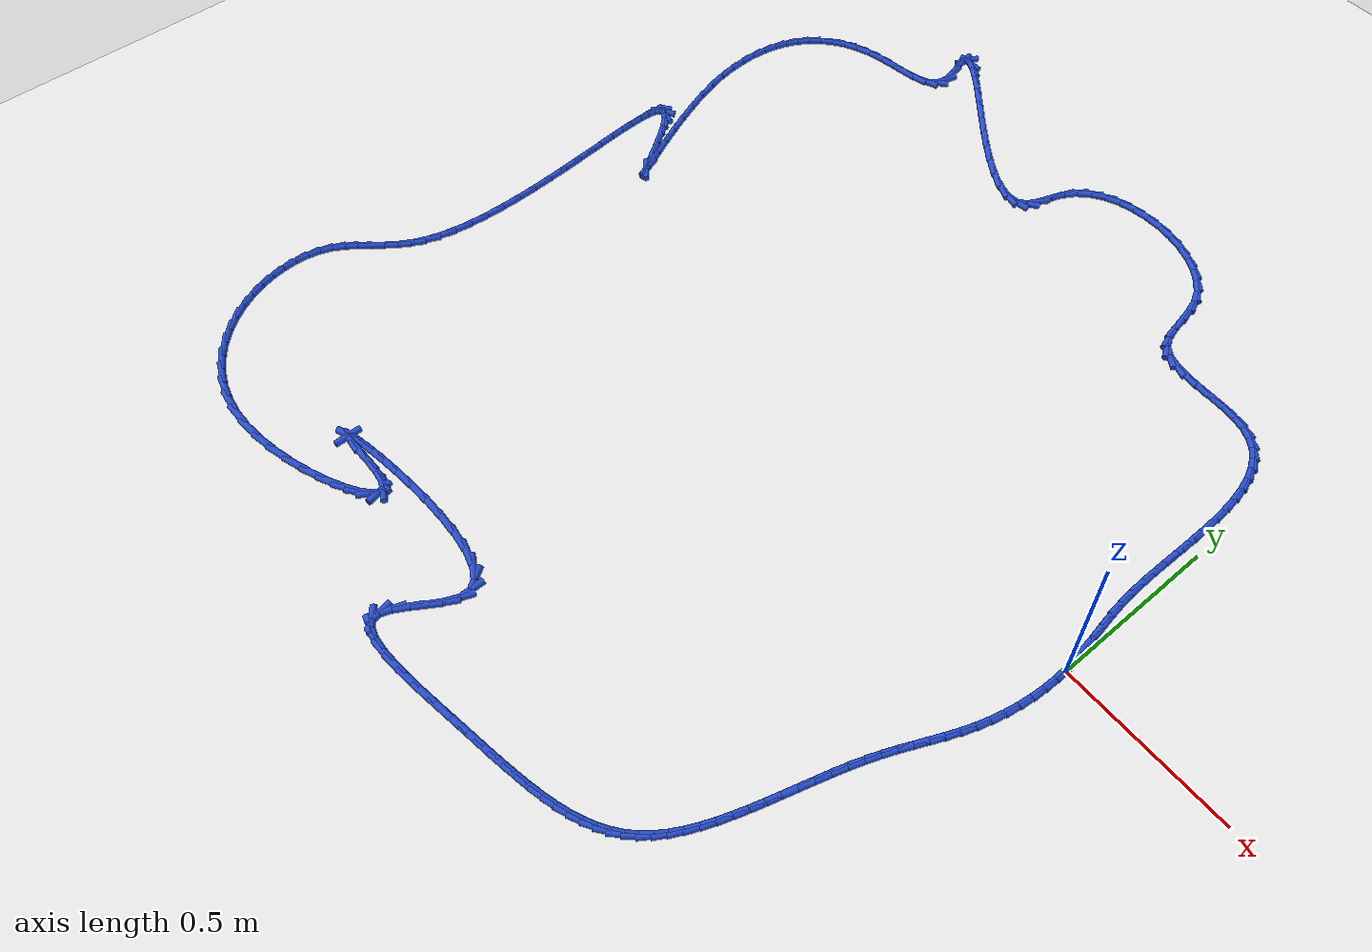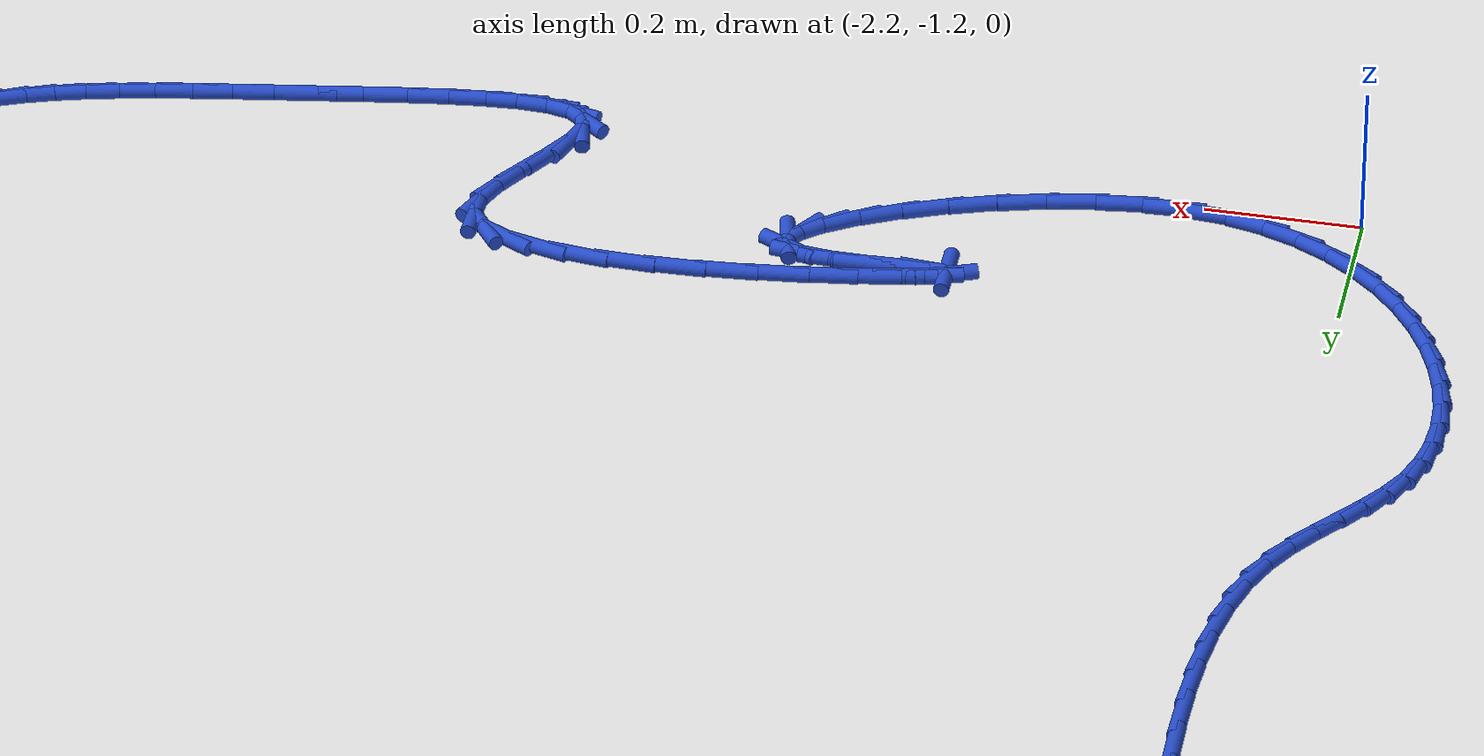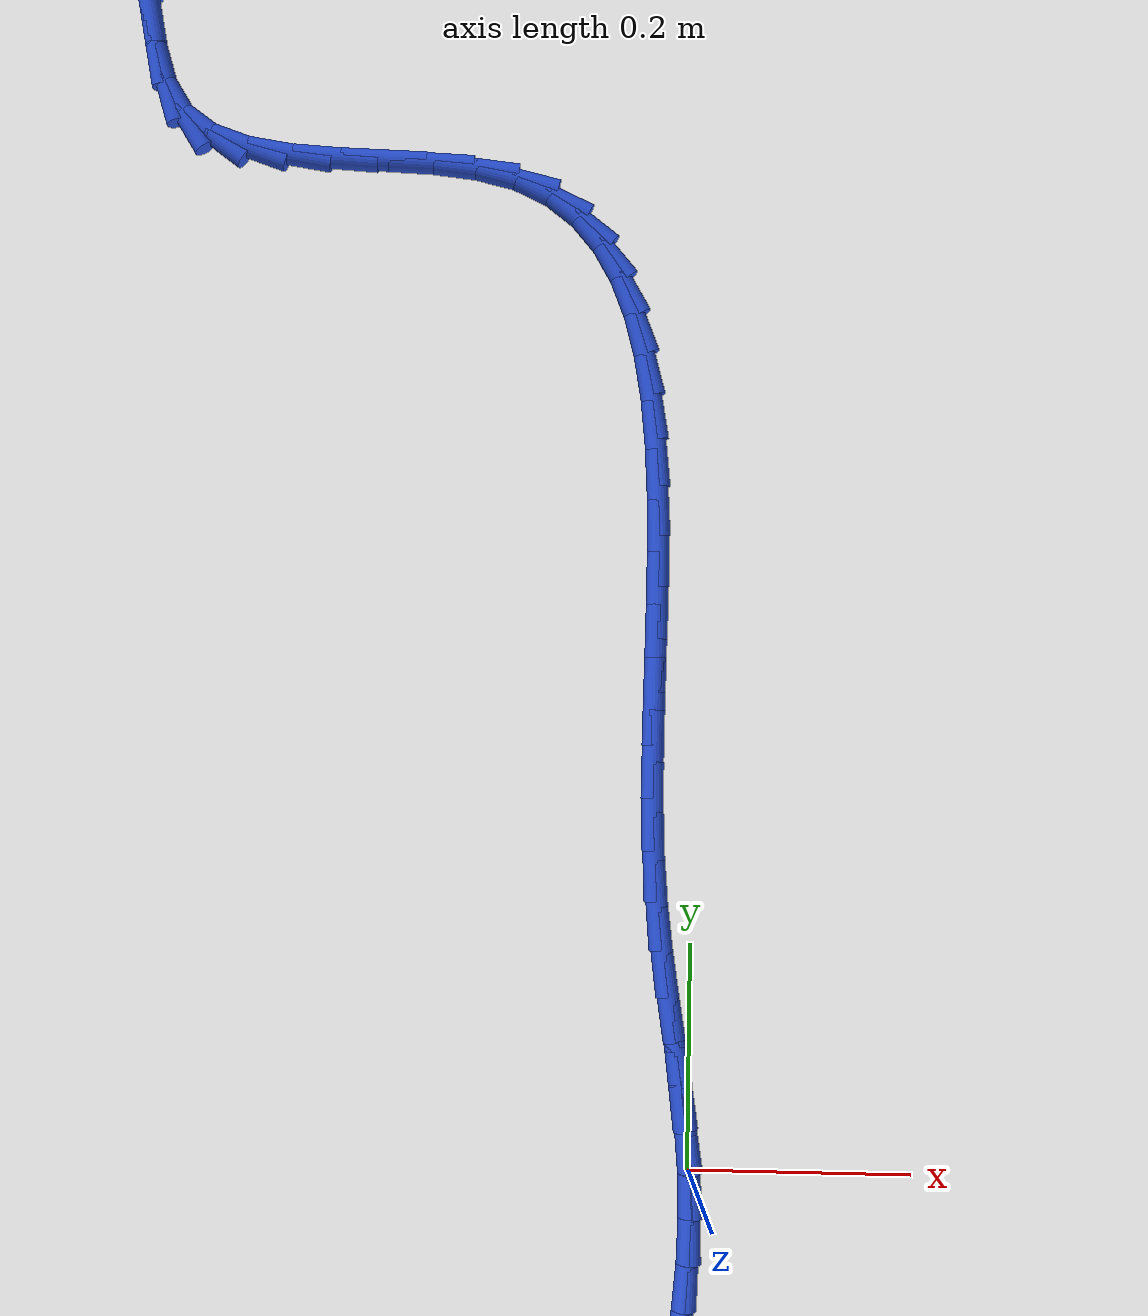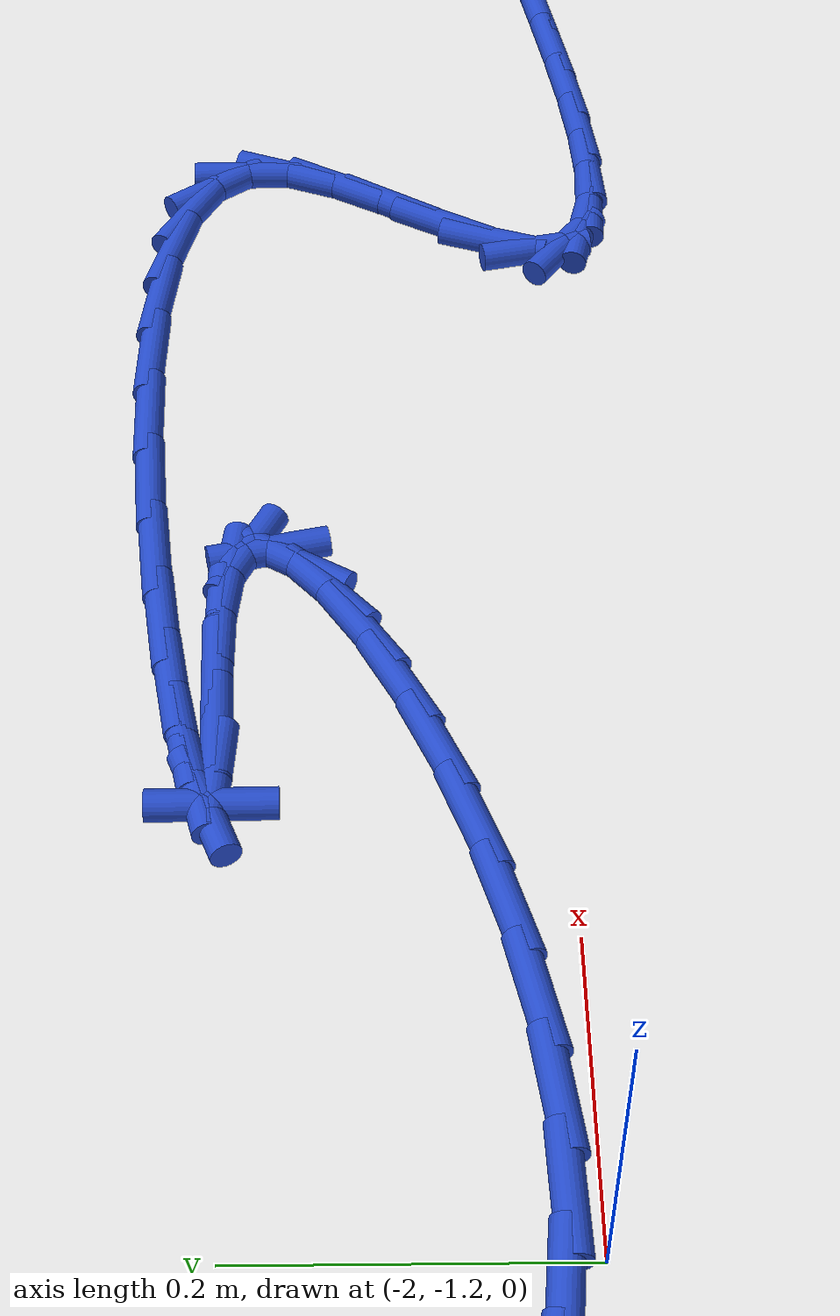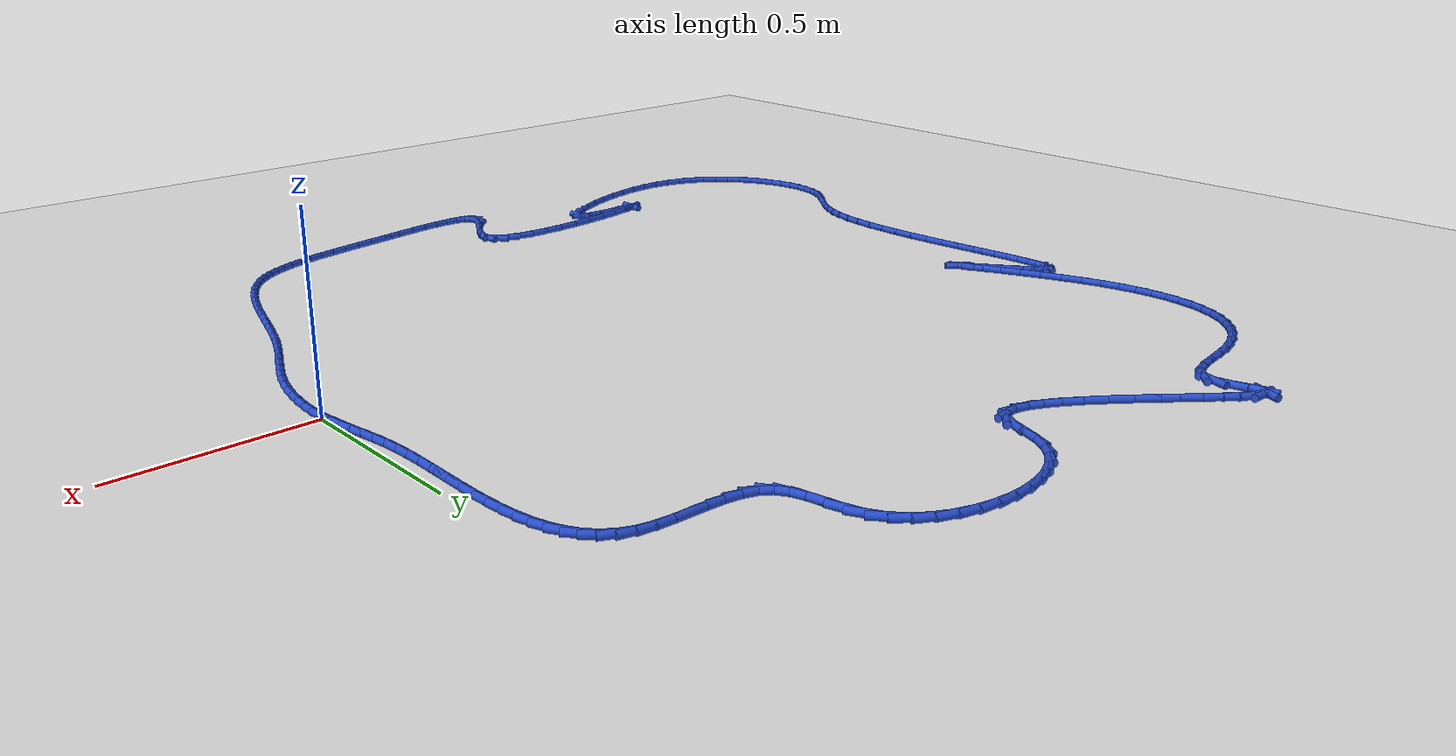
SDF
<sdf version="1.6">
 <world name="default">
  <light name="sun" type="directional">
   <pose>0 0 10 0 -0 0</pose>
   <diffuse>0.8 0.8 0.8 1</diffuse>
   <specular>0.2 0.2 0.2 1</specular>
   <attenuation>
    <range>1000</range>
    <constant>0.9</constant>
    <linear>0.01</linear>
    <quadratic>0.001</quadratic>
   </attenuation>
   <direction>-0.5 0.1 -0.9</direction>
  </light>
  <model name="ground_plane">
   <static>1</static>
   <link name="link">
    <collision name="collision">
     <geometry><plane><normal>0 0 1</normal><size>100 100</size></plane></geometry>
     <surface><friction><ode><mu>100</mu><mu2>50</mu2></ode></friction></surface>
    </collision>
    <visual name="visual">
     <cast_shadows>0</cast_shadows>
     <geometry><plane><normal>0 0 1</normal><size>100 100</size></plane></geometry>
     <material>
      <script><uri>file://media/materials/scripts/gazebo.material</uri><name>Gazebo/WhiteGlow</name></script>
     </material>
    </visual>
   </link>
  </model>
  <gravity>0 0 -9.8</gravity>
  <magnetic_field>6e-06 2.3e-05 -4.2e-05</magnetic_field>
  <atmosphere type="adiabatic"/>
  <physics name="default_physics" default="0" type="ode">
   <max_step_size>0.001</max_step_size>
   <real_time_factor>1</real_time_factor>
   <real_time_update_rate>1000</real_time_update_rate>
  </physics>
  <scene><ambient>0.4 0.4 0.4 1</ambient><background>0.7 0.7 0.7 1</background><shadows>1</shadows></scene>
  <spherical_coordinates>
   <surface_model>EARTH_WGS84</surface_model>
   <latitude_deg>0</latitude_deg>
   <longitude_deg>0</longitude_deg>
   <elevation>0</elevation>
   <heading_deg>0</heading_deg>
  </spherical_coordinates>
  <model name="line">
   <link name="link_0">
    <pose>-1.5612511283791264e-17 -4.85722573273506e-17 0.01 0 1.57 -1.4862448702870033</pose>
    <collision name="collision">
     <geometry><cylinder><radius>0.01</radius><length>0.08</length></cylinder></geometry>
    </collision>
    <visual name="visual">
     <material>
      <script><name>Gazebo/Blue</name><uri>file://media/materials/scripts/gazebo.material</uri></script>
     </material>
     <geometry><cylinder><radius>0.01</radius><length>0.08</length></cylinder></geometry>
    </visual>
   </link>
   <link name="link_1">
    <pose>-0.003258718003331035 0.038449353384300416 0.01 0 1.57 -1.4411728537391673</pose>
    <collision name="collision">
     <geometry><cylinder><radius>0.01</radius><length>0.08</length></cylinder></geometry>
    </collision>
    <visual name="visual">
     <material>
      <script><name>Gazebo/Blue</name><uri>file://media/materials/scripts/gazebo.material</uri></script>
     </material>
     <geometry><cylinder><radius>0.01</radius><length>0.08</length></cylinder></geometry>
    </visual>
   </link>
   <link name="link_2">
    <pose>-0.008221410162932275 0.07652012922128243 0.01 0 1.57 -1.4147956920683136</pose>
    <collision name="collision">
     <geometry><cylinder><radius>0.01</radius><length>0.08</length></cylinder></geometry>
    </collision>
    <visual name="visual">
     <material>
      <script><name>Gazebo/Blue</name><uri>file://media/materials/scripts/gazebo.material</uri></script>
     </material>
     <geometry><cylinder><radius>0.01</radius><length>0.08</length></cylinder></geometry>
    </visual>
   </link>
   <link name="link_3">
    <pose>-0.014224010775536464 0.11468553762563367 0.01 0 1.57 -1.407584973718065</pose>
    <collision name="collision">
     <geometry><cylinder><radius>0.01</radius><length>0.08</length></cylinder></geometry>
    </collision>
    <visual name="visual">
     <material>
      <script><name>Gazebo/Blue</name><uri>file://media/materials/scripts/gazebo.material</uri></script>
     </material>
     <geometry><cylinder><radius>0.01</radius><length>0.08</length></cylinder></geometry>
    </visual>
   </link>
   <link name="link_4">
    <pose>-0.020602454137876286 0.15341878871204168 0.01 0 1.57 -1.418856955793478</pose>
    <collision name="collision">
     <geometry><cylinder><radius>0.01</radius><length>0.08</length></cylinder></geometry>
    </collision>
    <visual name="visual">
     <material>
      <script><name>Gazebo/Blue</name><uri>file://media/materials/scripts/gazebo.material</uri></script>
     </material>
     <geometry><cylinder><radius>0.01</radius><length>0.08</length></cylinder></geometry>
    </visual>
   </link>
   <link name="link_5">
    <pose>-0.026692674546684465 0.19319309259519418 0.01 0 1.57 -1.4469931721940654</pose>
    <collision name="collision">
     <geometry><cylinder><radius>0.01</radius><length>0.08</length></cylinder></geometry>
    </collision>
    <visual name="visual">
     <material>
      <script><name>Gazebo/Blue</name><uri>file://media/materials/scripts/gazebo.material</uri></script>
     </material>
     <geometry><cylinder><radius>0.01</radius><length>0.08</length></cylinder></geometry>
    </visual>
   </link>
   <link name="link_6">
    <pose>-0.03183060629869373 0.23448165938977883 0.01 0 1.57 -1.4892259229793225</pose>
    <collision name="collision">
     <geometry><cylinder><radius>0.01</radius><length>0.08</length></cylinder></geometry>
    </collision>
    <visual name="visual">
     <material>
      <script><name>Gazebo/Blue</name><uri>file://media/materials/scripts/gazebo.material</uri></script>
     </material>
     <geometry><cylinder><radius>0.01</radius><length>0.08</length></cylinder></geometry>
    </visual>
   </link>
   <link name="link_7">
    <pose>-0.03536742958510055 0.2777445989224827 0.01 0 1.57 -1.5314287881267932</pose>
    <collision name="collision">
     <geometry><cylinder><radius>0.01</radius><length>0.08</length></cylinder></geometry>
    </collision>
    <visual name="visual">
     <material>
      <script><name>Gazebo/Blue</name><uri>file://media/materials/scripts/gazebo.material</uri></script>
     </material>
     <geometry><cylinder><radius>0.01</radius><length>0.08</length></cylinder></geometry>
    </visual>
   </link>
   <link name="link_8">
    <pose>-0.037150559631188164 0.3230156228261835 0.01 0 1.57 -1.5607406526389505</pose>
    <collision name="collision">
     <geometry><cylinder><radius>0.01</radius><length>0.08</length></cylinder></geometry>
    </collision>
    <visual name="visual">
     <material>
      <script><name>Gazebo/Blue</name><uri>file://media/materials/scripts/gazebo.material</uri></script>
     </material>
     <geometry><cylinder><radius>0.01</radius><length>0.08</length></cylinder></geometry>
    </visual>
   </link>
   <link name="link_9">
    <pose>-0.03762120710262899 0.3698182141406869 0.01 0 1.57 1.563150907946527</pose>
    <collision name="collision">
     <geometry><cylinder><radius>0.01</radius><length>0.08</length></cylinder></geometry>
    </collision>
    <visual name="visual">
     <material>
      <script><name>Gazebo/Blue</name><uri>file://media/materials/scripts/gazebo.material</uri></script>
     </material>
     <geometry><cylinder><radius>0.01</radius><length>0.08</length></cylinder></geometry>
    </visual>
   </link>
   <link name="link_10">
    <pose>-0.03725553789822558 0.41764582004124523 0.01 0 1.57 1.5557844448993894</pose>
    <collision name="collision">
     <geometry><cylinder><radius>0.01</radius><length>0.08</length></cylinder></geometry>
    </collision>
    <visual name="visual">
     <material>
      <script><name>Gazebo/Blue</name><uri>file://media/materials/scripts/gazebo.material</uri></script>
     </material>
     <geometry><cylinder><radius>0.01</radius><length>0.08</length></cylinder></geometry>
    </visual>
   </link>
   <link name="link_11">
    <pose>-0.03652971791678038 0.4659918877031102 0.01 0 1.57 1.5581867723345757</pose>
    <collision name="collision">
     <geometry><cylinder><radius>0.01</radius><length>0.08</length></cylinder></geometry>
    </collision>
    <visual name="visual">
     <material>
      <script><name>Gazebo/Blue</name><uri>file://media/materials/scripts/gazebo.material</uri></script>
     </material>
     <geometry><cylinder><radius>0.01</radius><length>0.08</length></cylinder></geometry>
    </visual>
   </link>
   <link name="link_12">
    <pose>-0.0359199130570959 0.514349864301534 0.01 0 1.57 1.5704281151111956</pose>
    <collision name="collision">
     <geometry><cylinder><radius>0.01</radius><length>0.08</length></cylinder></geometry>
    </collision>
    <visual name="visual">
     <material>
      <script><name>Gazebo/Blue</name><uri>file://media/materials/scripts/gazebo.material</uri></script>
     </material>
     <geometry><cylinder><radius>0.01</radius><length>0.08</length></cylinder></geometry>
    </visual>
   </link>
   <link name="link_13">
    <pose>-0.03590228921797464 0.5622131970117685 0.01 0 1.57 -1.5483785040625784</pose>
    <collision name="collision">
     <geometry><cylinder><radius>0.01</radius><length>0.08</length></cylinder></geometry>
    </collision>
    <visual name="visual">
     <material>
      <script><name>Gazebo/Blue</name><uri>file://media/materials/scripts/gazebo.material</uri></script>
     </material>
     <geometry><cylinder><radius>0.01</radius><length>0.08</length></cylinder></geometry>
    </visual>
   </link>
   <link name="link_14">
    <pose>-0.036953012298219096 0.6090753330090657 0.01 0 1.57 -1.5136373803837875</pose>
    <collision name="collision">
     <geometry><cylinder><radius>0.01</radius><length>0.08</length></cylinder></geometry>
    </collision>
    <visual name="visual">
     <material>
      <script><name>Gazebo/Blue</name><uri>file://media/materials/scripts/gazebo.material</uri></script>
     </material>
     <geometry><cylinder><radius>0.01</radius><length>0.08</length></cylinder></geometry>
    </visual>
   </link>
   <link name="link_15">
    <pose>-0.03954824819663176 0.6544297194686776 0.01 0 1.57 -1.4646917946296698</pose>
    <collision name="collision">
     <geometry><cylinder><radius>0.01</radius><length>0.08</length></cylinder></geometry>
    </collision>
    <visual name="visual">
     <material>
      <script><name>Gazebo/Blue</name><uri>file://media/materials/scripts/gazebo.material</uri></script>
     </material>
     <geometry><cylinder><radius>0.01</radius><length>0.08</length></cylinder></geometry>
    </visual>
   </link>
   <link name="link_16">
    <pose>-0.04416416281201512 0.6977698035658562 0.01 0 1.57 -1.3982782623419683</pose>
    <collision name="collision">
     <geometry><cylinder><radius>0.01</radius><length>0.08</length></cylinder></geometry>
    </collision>
    <visual name="visual">
     <material>
      <script><name>Gazebo/Blue</name><uri>file://media/materials/scripts/gazebo.material</uri></script>
     </material>
     <geometry><cylinder><radius>0.01</radius><length>0.08</length></cylinder></geometry>
    </visual>
   </link>
   <link name="link_17">
    <pose>-0.051276922043171656 0.7385890324758535 0.01 0 1.57 -1.3099975276250433</pose>
    <collision name="collision">
     <geometry><cylinder><radius>0.01</radius><length>0.08</length></cylinder></geometry>
    </collision>
    <visual name="visual">
     <material>
      <script><name>Gazebo/Blue</name><uri>file://media/materials/scripts/gazebo.material</uri></script>
     </material>
     <geometry><cylinder><radius>0.01</radius><length>0.08</length></cylinder></geometry>
    </visual>
   </link>
   <link name="link_18">
    <pose>-0.061362691788903884 0.7763808533739213 0.01 0 1.57 -1.1945296538129013</pose>
    <collision name="collision">
     <geometry><cylinder><radius>0.01</radius><length>0.08</length></cylinder></geometry>
    </collision>
    <visual name="visual">
     <material>
      <script><name>Gazebo/Blue</name><uri>file://media/materials/scripts/gazebo.material</uri></script>
     </material>
     <geometry><cylinder><radius>0.01</radius><length>0.08</length></cylinder></geometry>
    </visual>
   </link>
   <link name="link_19">
    <pose>-0.0748976379480143 0.8106387134353118 0.01 0 1.57 -1.0468428096407503</pose>
    <collision name="collision">
     <geometry><cylinder><radius>0.01</radius><length>0.08</length></cylinder></geometry>
    </collision>
    <visual name="visual">
     <material>
      <script><name>Gazebo/Blue</name><uri>file://media/materials/scripts/gazebo.material</uri></script>
     </material>
     <geometry><cylinder><radius>0.01</radius><length>0.08</length></cylinder></geometry>
    </visual>
   </link>
   <link name="link_20">
    <pose>-0.09235792641930539 0.840856059835277 0.01 0 1.57 -0.8653518427793409</pose>
    <collision name="collision">
     <geometry><cylinder><radius>0.01</radius><length>0.08</length></cylinder></geometry>
    </collision>
    <visual name="visual">
     <material>
      <script><name>Gazebo/Blue</name><uri>file://media/materials/scripts/gazebo.material</uri></script>
     </material>
     <geometry><cylinder><radius>0.01</radius><length>0.08</length></cylinder></geometry>
    </visual>
   </link>
   <link name="link_21">
    <pose>-0.11421972310157957 0.8665263397490685 0.01 0 1.57 -0.6568185991958423</pose>
    <collision name="collision">
     <geometry><cylinder><radius>0.01</radius><length>0.08</length></cylinder></geometry>
    </collision>
    <visual name="visual">
     <material>
      <script><name>Gazebo/Blue</name><uri>file://media/materials/scripts/gazebo.material</uri></script>
     </material>
     <geometry><cylinder><radius>0.01</radius><length>0.08</length></cylinder></geometry>
    </visual>
   </link>
   <link name="link_22">
    <pose>-0.14095919389363945 0.8871430003519389 0.01 0 1.57 -0.43866219690416813</pose>
    <collision name="collision">
     <geometry><cylinder><radius>0.01</radius><length>0.08</length></cylinder></geometry>
    </collision>
    <visual name="visual">
     <material>
      <script><name>Gazebo/Blue</name><uri>file://media/materials/scripts/gazebo.material</uri></script>
     </material>
     <geometry><cylinder><radius>0.01</radius><length>0.08</length></cylinder></geometry>
    </visual>
   </link>
   <link name="link_23">
    <pose>-0.17305250469428757 0.90219948881914 0.01 0 1.57 -0.2383044312807469</pose>
    <collision name="collision">
     <geometry><cylinder><radius>0.01</radius><length>0.08</length></cylinder></geometry>
    </collision>
    <visual name="visual">
     <material>
      <script><name>Gazebo/Blue</name><uri>file://media/materials/scripts/gazebo.material</uri></script>
     </material>
     <geometry><cylinder><radius>0.01</radius><length>0.08</length></cylinder></geometry>
    </visual>
   </link>
   <link name="link_24">
    <pose>-0.21080017339107024 0.9113691651961542 0.01 0 1.57 -0.10668738232148889</pose>
    <collision name="collision">
     <geometry><cylinder><radius>0.01</radius><length>0.08</length></cylinder></geometry>
    </collision>
    <visual name="visual">
     <material>
      <script><name>Gazebo/Blue</name><uri>file://media/materials/scripts/gazebo.material</uri></script>
     </material>
     <geometry><cylinder><radius>0.01</radius><length>0.08</length></cylinder></geometry>
    </visual>
   </link>
   <link name="link_25">
    <pose>-0.2529788580198435 0.9158862497840748 0.01 0 1.57 -0.042577228251818686</pose>
    <collision name="collision">
     <geometry><cylinder><radius>0.01</radius><length>0.08</length></cylinder></geometry>
    </collision>
    <visual name="visual">
     <material>
      <script><name>Gazebo/Blue</name><uri>file://media/materials/scripts/gazebo.material</uri></script>
     </material>
     <geometry><cylinder><radius>0.01</radius><length>0.08</length></cylinder></geometry>
    </visual>
   </link>
   <link name="link_26">
    <pose>-0.29758267507103575 0.9177865050962073 0.01 0 1.57 -0.029441684997133778</pose>
    <collision name="collision">
     <geometry><cylinder><radius>0.01</radius><length>0.08</length></cylinder></geometry>
    </collision>
    <visual name="visual">
     <material>
      <script><name>Gazebo/Blue</name><uri>file://media/materials/scripts/gazebo.material</uri></script>
     </material>
     <geometry><cylinder><radius>0.01</radius><length>0.08</length></cylinder></geometry>
    </visual>
   </link>
   <link name="link_27">
    <pose>-0.3425993356885788 0.9191122545187329 0.01 0 1.57 -0.06425380756421745</pose>
    <collision name="collision">
     <geometry><cylinder><radius>0.01</radius><length>0.08</length></cylinder></geometry>
    </collision>
    <visual name="visual">
     <material>
      <script><name>Gazebo/Blue</name><uri>file://media/materials/scripts/gazebo.material</uri></script>
     </material>
     <geometry><cylinder><radius>0.01</radius><length>0.08</length></cylinder></geometry>
    </visual>
   </link>
   <link name="link_28">
    <pose>-0.38601655101640436 0.921905821437833 0.01 0 1.57 -0.15705853035319087</pose>
    <collision name="collision">
     <geometry><cylinder><radius>0.01</radius><length>0.08</length></cylinder></geometry>
    </collision>
    <visual name="visual">
     <material>
      <script><name>Gazebo/Blue</name><uri>file://media/materials/scripts/gazebo.material</uri></script>
     </material>
     <geometry><cylinder><radius>0.01</radius><length>0.08</length></cylinder></geometry>
    </visual>
   </link>
   <link name="link_29">
    <pose>-0.42582203219844467 0.9282095292396894 0.01 0 1.57 -0.3338745355398296</pose>
    <collision name="collision">
     <geometry><cylinder><radius>0.01</radius><length>0.08</length></cylinder></geometry>
    </collision>
    <visual name="visual">
     <material>
      <script><name>Gazebo/Blue</name><uri>file://media/materials/scripts/gazebo.material</uri></script>
     </material>
     <geometry><cylinder><radius>0.01</radius><length>0.08</length></cylinder></geometry>
    </visual>
   </link>
   <link name="link_30">
    <pose>-0.46000349037863153 0.9400657013104841 0.01 0 1.57 -0.6323694863271845</pose>
    <collision name="collision">
     <geometry><cylinder><radius>0.01</radius><length>0.08</length></cylinder></geometry>
    </collision>
    <visual name="visual">
     <material>
      <script><name>Gazebo/Blue</name><uri>file://media/materials/scripts/gazebo.material</uri></script>
     </material>
     <geometry><cylinder><radius>0.01</radius><length>0.08</length></cylinder></geometry>
    </visual>
   </link>
   <link name="link_31">
    <pose>-0.4865486367008969 0.9595166610363981 0.01 0 1.57 -1.018316951791573</pose>
    <collision name="collision">
     <geometry><cylinder><radius>0.01</radius><length>0.08</length></cylinder></geometry>
    </collision>
    <visual name="visual">
     <material>
      <script><name>Gazebo/Blue</name><uri>file://media/materials/scripts/gazebo.material</uri></script>
     </material>
     <geometry><cylinder><radius>0.01</radius><length>0.08</length></cylinder></geometry>
    </visual>
   </link>
   <link name="link_32">
    <pose>-0.5041212802929735 0.9880195365777795 0.01 0 1.57 -1.2750928583027492</pose>
    <collision name="collision">
     <geometry><cylinder><radius>0.01</radius><length>0.08</length></cylinder></geometry>
    </collision>
    <visual name="visual">
     <material>
      <script><name>Gazebo/Blue</name><uri>file://media/materials/scripts/gazebo.material</uri></script>
     </material>
     <geometry><cylinder><radius>0.01</radius><length>0.08</length></cylinder></geometry>
    </visual>
   </link>
   <link name="link_33">
    <pose>-0.5150415776935554 1.0238667120783544 0.01 0 1.57 -1.379720333185816</pose>
    <collision name="collision">
     <geometry><cylinder><radius>0.01</radius><length>0.08</length></cylinder></geometry>
    </collision>
    <visual name="visual">
     <material>
      <script><name>Gazebo/Blue</name><uri>file://media/materials/scripts/gazebo.material</uri></script>
     </material>
     <geometry><cylinder><radius>0.01</radius><length>0.08</length></cylinder></geometry>
    </visual>
   </link>
   <link name="link_34">
    <pose>-0.5228600468036078 1.0642856349234142 0.01 0 1.57 -1.377398346864367</pose>
    <collision name="collision">
     <geometry><cylinder><radius>0.01</radius><length>0.08</length></cylinder></geometry>
    </collision>
    <visual name="visual">
     <material>
      <script><name>Gazebo/Blue</name><uri>file://media/materials/scripts/gazebo.material</uri></script>
     </material>
     <geometry><cylinder><radius>0.01</radius><length>0.08</length></cylinder></geometry>
    </visual>
   </link>
   <link name="link_35">
    <pose>-0.5311281315239995 1.106502951000932 0.01 0 1.57 -1.2816448529172568</pose>
    <collision name="collision">
     <geometry><cylinder><radius>0.01</radius><length>0.08</length></cylinder></geometry>
    </collision>
    <visual name="visual">
     <material>
      <script><name>Gazebo/Blue</name><uri>file://media/materials/scripts/gazebo.material</uri></script>
     </material>
     <geometry><cylinder><radius>0.01</radius><length>0.08</length></cylinder></geometry>
    </visual>
   </link>
   <link name="link_36">
    <pose>-0.5433972757555996 1.1477453061988785 0.01 0 1.57 -1.0886192543655673</pose>
    <collision name="collision">
     <geometry><cylinder><radius>0.01</radius><length>0.08</length></cylinder></geometry>
    </collision>
    <visual name="visual">
     <material>
      <script><name>Gazebo/Blue</name><uri>file://media/materials/scripts/gazebo.material</uri></script>
     </material>
     <geometry><cylinder><radius>0.01</radius><length>0.08</length></cylinder></geometry>
    </visual>
   </link>
   <link name="link_37">
    <pose>-0.5630645112711433 1.1853225793798068 0.01 0 1.57 -0.8631332786445037</pose>
    <collision name="collision">
     <geometry><cylinder><radius>0.01</radius><length>0.08</length></cylinder></geometry>
    </collision>
    <visual name="visual">
     <material>
      <script><name>Gazebo/Blue</name><uri>file://media/materials/scripts/gazebo.material</uri></script>
     </material>
     <geometry><cylinder><radius>0.01</radius><length>0.08</length></cylinder></geometry>
    </visual>
   </link>
   <link name="link_38">
    <pose>-0.5909585028613503 1.2179290796729252 0.01 0 1.57 -0.6678142674106703</pose>
    <collision name="collision">
     <geometry><cylinder><radius>0.01</radius><length>0.08</length></cylinder></geometry>
    </collision>
    <visual name="visual">
     <material>
      <script><name>Gazebo/Blue</name><uri>file://media/materials/scripts/gazebo.material</uri></script>
     </material>
     <geometry><cylinder><radius>0.01</radius><length>0.08</length></cylinder></geometry>
    </visual>
   </link>
   <link name="link_39">
    <pose>-0.6257899730940383 1.2454007534177607 0.01 0 1.57 -0.5024229894165705</pose>
    <collision name="collision">
     <geometry><cylinder><radius>0.01</radius><length>0.08</length></cylinder></geometry>
    </collision>
    <visual name="visual">
     <material>
      <script><name>Gazebo/Blue</name><uri>file://media/materials/scripts/gazebo.material</uri></script>
     </material>
     <geometry><cylinder><radius>0.01</radius><length>0.08</length></cylinder></geometry>
    </visual>
   </link>
   <link name="link_40">
    <pose>-0.6662063686550959 1.2676076546365418 0.01 0 1.57 -0.36012278649121715</pose>
    <collision name="collision">
     <geometry><cylinder><radius>0.01</radius><length>0.08</length></cylinder></geometry>
    </collision>
    <visual name="visual">
     <material>
      <script><name>Gazebo/Blue</name><uri>file://media/materials/scripts/gazebo.material</uri></script>
     </material>
     <geometry><cylinder><radius>0.01</radius><length>0.08</length></cylinder></geometry>
    </visual>
   </link>
   <link name="link_41">
    <pose>-0.710855136230413 1.2844198373514986 0.01 0 1.57 -0.23316942395733173</pose>
    <collision name="collision">
     <geometry><cylinder><radius>0.01</radius><length>0.08</length></cylinder></geometry>
    </collision>
    <visual name="visual">
     <material>
      <script><name>Gazebo/Blue</name><uri>file://media/materials/scripts/gazebo.material</uri></script>
     </material>
     <geometry><cylinder><radius>0.01</radius><length>0.08</length></cylinder></geometry>
    </visual>
   </link>
   <link name="link_42">
    <pose>-0.7583837225058784 1.2957073555848606 0.01 0 1.57 -0.11432570797332499</pose>
    <collision name="collision">
     <geometry><cylinder><radius>0.01</radius><length>0.08</length></cylinder></geometry>
    </collision>
    <visual name="visual">
     <material>
      <script><name>Gazebo/Blue</name><uri>file://media/materials/scripts/gazebo.material</uri></script>
     </material>
     <geometry><cylinder><radius>0.01</radius><length>0.08</length></cylinder></geometry>
    </visual>
   </link>
   <link name="link_43">
    <pose>-0.807439574167382 1.3013402633588576 0.01 0 1.57 0.003080366585114261</pose>
    <collision name="collision">
     <geometry><cylinder><radius>0.01</radius><length>0.08</length></cylinder></geometry>
    </collision>
    <visual name="visual">
     <material>
      <script><name>Gazebo/Blue</name><uri>file://media/materials/scripts/gazebo.material</uri></script>
     </material>
     <geometry><cylinder><radius>0.01</radius><length>0.08</length></cylinder></geometry>
    </visual>
   </link>
   <link name="link_44">
    <pose>-0.8566701379008121 1.301188614695719 0.01 0 1.57 0.12557522661740173</pose>
    <collision name="collision">
     <geometry><cylinder><radius>0.01</radius><length>0.08</length></cylinder></geometry>
    </collision>
    <visual name="visual">
     <material>
      <script><name>Gazebo/Blue</name><uri>file://media/materials/scripts/gazebo.material</uri></script>
     </material>
     <geometry><cylinder><radius>0.01</radius><length>0.08</length></cylinder></geometry>
    </visual>
   </link>
   <link name="link_45">
    <pose>-0.9047228603920594 1.295122463617675 0.01 0 1.57 0.26001394244173315</pose>
    <collision name="collision">
     <geometry><cylinder><radius>0.01</radius><length>0.08</length></cylinder></geometry>
    </collision>
    <visual name="visual">
     <material>
      <script><name>Gazebo/Blue</name><uri>file://media/materials/scripts/gazebo.material</uri></script>
     </material>
     <geometry><cylinder><radius>0.01</radius><length>0.08</length></cylinder></geometry>
    </visual>
   </link>
   <link name="link_46">
    <pose>-0.950245188327012 1.283011864146955 0.01 0 1.57 0.41377559666240427</pose>
    <collision name="collision">
     <geometry><cylinder><radius>0.01</radius><length>0.08</length></cylinder></geometry>
    </collision>
    <visual name="visual">
     <material>
      <script><name>Gazebo/Blue</name><uri>file://media/materials/scripts/gazebo.material</uri></script>
     </material>
     <geometry><cylinder><radius>0.01</radius><length>0.08</length></cylinder></geometry>
    </visual>
   </link>
   <link name="link_47">
    <pose>-0.9918845683915597 1.2647268703057886 0.01 0 1.57 0.59406505190191</pose>
    <collision name="collision">
     <geometry><cylinder><radius>0.01</radius><length>0.08</length></cylinder></geometry>
    </collision>
    <visual name="visual">
     <material>
      <script><name>Gazebo/Blue</name><uri>file://media/materials/scripts/gazebo.material</uri></script>
     </material>
     <geometry><cylinder><radius>0.01</radius><length>0.08</length></cylinder></geometry>
    </visual>
   </link>
   <link name="link_48">
    <pose>-1.028288447271592 1.240137536116406 0.01 0 1.57 0.8052477446286561</pose>
    <collision name="collision">
     <geometry><cylinder><radius>0.01</radius><length>0.08</length></cylinder></geometry>
    </collision>
    <visual name="visual">
     <material>
      <script><name>Gazebo/Blue</name><uri>file://media/materials/scripts/gazebo.material</uri></script>
     </material>
     <geometry><cylinder><radius>0.01</radius><length>0.08</length></cylinder></geometry>
    </visual>
   </link>
   <link name="link_49">
    <pose>-1.0581042716529976 1.209113915601036 0.01 0 1.57 1.040384360212619</pose>
    <collision name="collision">
     <geometry><cylinder><radius>0.01</radius><length>0.08</length></cylinder></geometry>
    </collision>
    <visual name="visual">
     <material>
      <script><name>Gazebo/Blue</name><uri>file://media/materials/scripts/gazebo.material</uri></script>
     </material>
     <geometry><cylinder><radius>0.01</radius><length>0.08</length></cylinder></geometry>
    </visual>
   </link>
   <link name="link_50">
    <pose>-1.0800849661528944 1.1716342930377543 0.01 0 1.57 1.2072469409295552</pose>
    <collision name="collision">
     <geometry><cylinder><radius>0.01</radius><length>0.08</length></cylinder></geometry>
    </collision>
    <visual name="visual">
     <material>
      <script><name>Gazebo/Blue</name><uri>file://media/materials/scripts/gazebo.material</uri></script>
     </material>
     <geometry><cylinder><radius>0.01</radius><length>0.08</length></cylinder></geometry>
    </visual>
   </link>
   <link name="link_51">
    <pose>-1.095734877289373 1.1305001697777635 0.01 0 1.57 1.2311267569901967</pose>
    <collision name="collision">
     <geometry><cylinder><radius>0.01</radius><length>0.08</length></cylinder></geometry>
    </collision>
    <visual name="visual">
     <material>
      <script><name>Gazebo/Blue</name><uri>file://media/materials/scripts/gazebo.material</uri></script>
     </material>
     <geometry><cylinder><radius>0.01</radius><length>0.08</length></cylinder></geometry>
    </visual>
   </link>
   <link name="link_52">
    <pose>-1.1095037157275238 1.0915352671900094 0.01 0 1.57 1.079768653693937</pose>
    <collision name="collision">
     <geometry><cylinder><radius>0.01</radius><length>0.08</length></cylinder></geometry>
    </collision>
    <visual name="visual">
     <material>
      <script><name>Gazebo/Blue</name><uri>file://media/materials/scripts/gazebo.material</uri></script>
     </material>
     <geometry><cylinder><radius>0.01</radius><length>0.08</length></cylinder></geometry>
    </visual>
   </link>
   <link name="link_53">
    <pose>-1.1259855149364908 1.0607113953841394 0.01 0 1.57 0.6357463018794571</pose>
    <collision name="collision">
     <geometry><cylinder><radius>0.01</radius><length>0.08</length></cylinder></geometry>
    </collision>
    <visual name="visual">
     <material>
      <script><name>Gazebo/Blue</name><uri>file://media/materials/scripts/gazebo.material</uri></script>
     </material>
     <geometry><cylinder><radius>0.01</radius><length>0.08</length></cylinder></geometry>
    </visual>
   </link>
   <link name="link_54">
    <pose>-1.1493722763051606 1.0434530660826582 0.01 0 1.57 0.10055534122656933</pose>
    <collision name="collision">
     <geometry><cylinder><radius>0.01</radius><length>0.08</length></cylinder></geometry>
    </collision>
    <visual name="visual">
     <material>
      <script><name>Gazebo/Blue</name><uri>file://media/materials/scripts/gazebo.material</uri></script>
     </material>
     <geometry><cylinder><radius>0.01</radius><length>0.08</length></cylinder></geometry>
    </visual>
   </link>
   <link name="link_55">
    <pose>-1.1802922682106312 1.0403333738567366 0.01 0 1.57 -0.2386878936296153</pose>
    <collision name="collision">
     <geometry><cylinder><radius>0.01</radius><length>0.08</length></cylinder></geometry>
    </collision>
    <visual name="visual">
     <material>
      <script><name>Gazebo/Blue</name><uri>file://media/materials/scripts/gazebo.material</uri></script>
     </material>
     <geometry><cylinder><radius>0.01</radius><length>0.08</length></cylinder></geometry>
    </visual>
   </link>
   <link name="link_56">
    <pose>-1.2175110831985427 1.0493896965315868 0.01 0 1.57 -0.4273201772210817</pose>
    <collision name="collision">
     <geometry><cylinder><radius>0.01</radius><length>0.08</length></cylinder></geometry>
    </collision>
    <visual name="visual">
     <material>
      <script><name>Gazebo/Blue</name><uri>file://media/materials/scripts/gazebo.material</uri></script>
     </material>
     <geometry><cylinder><radius>0.01</radius><length>0.08</length></cylinder></geometry>
    </visual>
   </link>
   <link name="link_57">
    <pose>-1.2597780726802024 1.068637302386784 0.01 0 1.57 -0.5374684256696984</pose>
    <collision name="collision">
     <geometry><cylinder><radius>0.01</radius><length>0.08</length></cylinder></geometry>
    </collision>
    <visual name="visual">
     <material>
      <script><name>Gazebo/Blue</name><uri>file://media/materials/scripts/gazebo.material</uri></script>
     </material>
     <geometry><cylinder><radius>0.01</radius><length>0.08</length></cylinder></geometry>
    </visual>
   </link>
   <link name="link_58">
    <pose>-1.3058425880669164 1.096091459701903 0.01 0 1.57 -0.6058496450434656</pose>
    <collision name="collision">
     <geometry><cylinder><radius>0.01</radius><length>0.08</length></cylinder></geometry>
    </collision>
    <visual name="visual">
     <material>
      <script><name>Gazebo/Blue</name><uri>file://media/materials/scripts/gazebo.material</uri></script>
     </material>
     <geometry><cylinder><radius>0.01</radius><length>0.08</length></cylinder></geometry>
    </visual>
   </link>
   <link name="link_59">
    <pose>-1.3544539807699907 1.1297674367565178 0.01 0 1.57 -0.649657963590251</pose>
    <collision name="collision">
     <geometry><cylinder><radius>0.01</radius><length>0.08</length></cylinder></geometry>
    </collision>
    <visual name="visual">
     <material>
      <script><name>Gazebo/Blue</name><uri>file://media/materials/scripts/gazebo.material</uri></script>
     </material>
     <geometry><cylinder><radius>0.01</radius><length>0.08</length></cylinder></geometry>
    </visual>
   </link>
   <link name="link_60">
    <pose>-1.4043616022007324 1.1676805018302043 0.01 0 1.57 -0.6772122630782234</pose>
    <collision name="collision">
     <geometry><cylinder><radius>0.01</radius><length>0.08</length></cylinder></geometry>
    </collision>
    <visual name="visual">
     <material>
      <script><name>Gazebo/Blue</name><uri>file://media/materials/scripts/gazebo.material</uri></script>
     </material>
     <geometry><cylinder><radius>0.01</radius><length>0.08</length></cylinder></geometry>
    </visual>
   </link>
   <link name="link_61">
    <pose>-1.454314803770447 1.2078459232025367 0.01 0 1.57 -0.6924288077604496</pose>
    <collision name="collision">
     <geometry><cylinder><radius>0.01</radius><length>0.08</length></cylinder></geometry>
    </collision>
    <visual name="visual">
     <material>
      <script><name>Gazebo/Blue</name><uri>file://media/materials/scripts/gazebo.material</uri></script>
     </material>
     <geometry><cylinder><radius>0.01</radius><length>0.08</length></cylinder></geometry>
    </visual>
   </link>
   <link name="link_62">
    <pose>-1.503062936890442 1.2482789691530896 0.01 0 1.57 -0.696506769953217</pose>
    <collision name="collision">
     <geometry><cylinder><radius>0.01</radius><length>0.08</length></cylinder></geometry>
    </collision>
    <visual name="visual">
     <material>
      <script><name>Gazebo/Blue</name><uri>file://media/materials/scripts/gazebo.material</uri></script>
     </material>
     <geometry><cylinder><radius>0.01</radius><length>0.08</length></cylinder></geometry>
    </visual>
   </link>
   <link name="link_63">
    <pose>-1.5493553529720239 1.2869949079614385 0.01 0 1.57 -0.6881295943837525</pose>
    <collision name="collision">
     <geometry><cylinder><radius>0.01</radius><length>0.08</length></cylinder></geometry>
    </collision>
    <visual name="visual">
     <material>
      <script><name>Gazebo/Blue</name><uri>file://media/materials/scripts/gazebo.material</uri></script>
     </material>
     <geometry><cylinder><radius>0.01</radius><length>0.08</length></cylinder></geometry>
    </visual>
   </link>
   <link name="link_64">
    <pose>-1.5919414034264985 1.322009007907158 0.01 0 1.57 -0.6620441916939217</pose>
    <collision name="collision">
     <geometry><cylinder><radius>0.01</radius><length>0.08</length></cylinder></geometry>
    </collision>
    <visual name="visual">
     <material>
      <script><name>Gazebo/Blue</name><uri>file://media/materials/scripts/gazebo.material</uri></script>
     </material>
     <geometry><cylinder><radius>0.01</radius><length>0.08</length></cylinder></geometry>
    </visual>
   </link>
   <link name="link_65">
    <pose>-1.6295704396651718 1.351336537269822 0.01 0 1.57 -0.603454108480119</pose>
    <collision name="collision">
     <geometry><cylinder><radius>0.01</radius><length>0.08</length></cylinder></geometry>
    </collision>
    <visual name="visual">
     <material>
      <script><name>Gazebo/Blue</name><uri>file://media/materials/scripts/gazebo.material</uri></script>
     </material>
     <geometry><cylinder><radius>0.01</radius><length>0.08</length></cylinder></geometry>
    </visual>
   </link>
   <link name="link_66">
    <pose>-1.6609918130993515 1.3729927643290067 0.01 0 1.57 -0.46427044094737385</pose>
    <collision name="collision">
     <geometry><cylinder><radius>0.01</radius><length>0.08</length></cylinder></geometry>
    </collision>
    <visual name="visual">
     <material>
      <script><name>Gazebo/Blue</name><uri>file://media/materials/scripts/gazebo.material</uri></script>
     </material>
     <geometry><cylinder><radius>0.01</radius><length>0.08</length></cylinder></geometry>
    </visual>
   </link>
   <link name="link_67">
    <pose>-1.6849548751403436 1.3849929573642863 0.01 0 1.57 -0.023558305418138727</pose>
    <collision name="collision">
     <geometry><cylinder><radius>0.01</radius><length>0.08</length></cylinder></geometry>
    </collision>
    <visual name="visual">
     <material>
      <script><name>Gazebo/Blue</name><uri>file://media/materials/scripts/gazebo.material</uri></script>
     </material>
     <geometry><cylinder><radius>0.01</radius><length>0.08</length></cylinder></geometry>
    </visual>
   </link>
   <link name="link_68">
    <pose>-1.7002089771994535 1.3853523846552351 0.01 0 1.57 1.1910657350004212</pose>
    <collision name="collision">
     <geometry><cylinder><radius>0.01</radius><length>0.08</length></cylinder></geometry>
    </collision>
    <visual name="visual">
     <material>
      <script><name>Gazebo/Blue</name><uri>file://media/materials/scripts/gazebo.material</uri></script>
     </material>
     <geometry><cylinder><radius>0.01</radius><length>0.08</length></cylinder></geometry>
    </visual>
   </link>
   <link name="link_69">
    <pose>-1.7055034706879892 1.3720863144814288 0.01 0 1.57 -1.3738094278115962</pose>
    <collision name="collision">
     <geometry><cylinder><radius>0.01</radius><length>0.08</length></cylinder></geometry>
    </collision>
    <visual name="visual">
     <material>
      <script><name>Gazebo/Blue</name><uri>file://media/materials/scripts/gazebo.material</uri></script>
     </material>
     <geometry><cylinder><radius>0.01</radius><length>0.08</length></cylinder></geometry>
    </visual>
   </link>
   <link name="link_70">
    <pose>-1.6997788617533163 1.3434023202513277 0.01 0 1.57 -1.2800492155268295</pose>
    <collision name="collision">
     <geometry><cylinder><radius>0.01</radius><length>0.08</length></cylinder></geometry>
    </collision>
    <visual name="visual">
     <material>
      <script><name>Gazebo/Blue</name><uri>file://media/materials/scripts/gazebo.material</uri></script>
     </material>
     <geometry><cylinder><radius>0.01</radius><length>0.08</length></cylinder></geometry>
    </visual>
   </link>
   <link name="link_71">
    <pose>-1.6877990549691917 1.3033664197312258 0.01 0 1.57 -1.4064138033620186</pose>
    <collision name="collision">
     <geometry><cylinder><radius>0.01</radius><length>0.08</length></cylinder></geometry>
    </collision>
    <visual name="visual">
     <material>
      <script><name>Gazebo/Blue</name><uri>file://media/materials/scripts/gazebo.material</uri></script>
     </material>
     <geometry><cylinder><radius>0.01</radius><length>0.08</length></cylinder></geometry>
    </visual>
   </link>
   <link name="link_72">
    <pose>-1.6810753349352145 1.2628326172801607 0.01 0 1.57 1.2936013254377046</pose>
    <collision name="collision">
     <geometry><cylinder><radius>0.01</radius><length>0.08</length></cylinder></geometry>
    </collision>
    <visual name="visual">
     <material>
      <script><name>Gazebo/Blue</name><uri>file://media/materials/scripts/gazebo.material</uri></script>
     </material>
     <geometry><cylinder><radius>0.01</radius><length>0.08</length></cylinder></geometry>
    </visual>
   </link>
   <link name="link_73">
    <pose>-1.6899464772639958 1.2316532707385368 0.01 0 1.57 0.7038913856940222</pose>
    <collision name="collision">
     <geometry><cylinder><radius>0.01</radius><length>0.08</length></cylinder></geometry>
    </collision>
    <visual name="visual">
     <material>
      <script><name>Gazebo/Blue</name><uri>file://media/materials/scripts/gazebo.material</uri></script>
     </material>
     <geometry><cylinder><radius>0.01</radius><length>0.08</length></cylinder></geometry>
    </visual>
   </link>
   <link name="link_74">
    <pose>-1.7146514487593112 1.2106796784110245 0.01 0 1.57 0.35275751543562295</pose>
    <collision name="collision">
     <geometry><cylinder><radius>0.01</radius><length>0.08</length></cylinder></geometry>
    </collision>
    <visual name="visual">
     <material>
      <script><name>Gazebo/Blue</name><uri>file://media/materials/scripts/gazebo.material</uri></script>
     </material>
     <geometry><cylinder><radius>0.01</radius><length>0.08</length></cylinder></geometry>
    </visual>
   </link>
   <link name="link_75">
    <pose>-1.7513826894808617 1.1971568299259878 0.01 0 1.57 0.19416046898314018</pose>
    <collision name="collision">
     <geometry><cylinder><radius>0.01</radius><length>0.08</length></cylinder></geometry>
    </collision>
    <visual name="visual">
     <material>
      <script><name>Gazebo/Blue</name><uri>file://media/materials/scripts/gazebo.material</uri></script>
     </material>
     <geometry><cylinder><radius>0.01</radius><length>0.08</length></cylinder></geometry>
    </visual>
   </link>
   <link name="link_76">
    <pose>-1.7963218490262982 1.1883200983345672 0.01 0 1.57 0.13927924777305753</pose>
    <collision name="collision">
     <geometry><cylinder><radius>0.01</radius><length>0.08</length></cylinder></geometry>
    </collision>
    <visual name="visual">
     <material>
      <script><name>Gazebo/Blue</name><uri>file://media/materials/scripts/gazebo.material</uri></script>
     </material>
     <geometry><cylinder><radius>0.01</radius><length>0.08</length></cylinder></geometry>
    </visual>
   </link>
   <link name="link_77">
    <pose>-1.845650576993271 1.1814048566879034 0.01 0 1.57 0.1542437336826235</pose>
    <collision name="collision">
     <geometry><cylinder><radius>0.01</radius><length>0.08</length></cylinder></geometry>
    </collision>
    <visual name="visual">
     <material>
      <script><name>Gazebo/Blue</name><uri>file://media/materials/scripts/gazebo.material</uri></script>
     </material>
     <geometry><cylinder><radius>0.01</radius><length>0.08</length></cylinder></geometry>
    </visual>
   </link>
   <link name="link_78">
    <pose>-1.8955505229794314 1.1736464780371378 0.01 0 1.57 0.23334751588588448</pose>
    <collision name="collision">
     <geometry><cylinder><radius>0.01</radius><length>0.08</length></cylinder></geometry>
    </collision>
    <visual name="visual">
     <material>
      <script><name>Gazebo/Blue</name><uri>file://media/materials/scripts/gazebo.material</uri></script>
     </material>
     <geometry><cylinder><radius>0.01</radius><length>0.08</length></cylinder></geometry>
    </visual>
   </link>
   <link name="link_79">
    <pose>-1.942479698091653 1.1624924839200714 0.01 0 1.57 0.34392930912046815</pose>
    <collision name="collision">
     <geometry><cylinder><radius>0.01</radius><length>0.08</length></cylinder></geometry>
    </collision>
    <visual name="visual">
     <material>
      <script><name>Gazebo/Blue</name><uri>file://media/materials/scripts/gazebo.material</uri></script>
     </material>
     <geometry><cylinder><radius>0.01</radius><length>0.08</length></cylinder></geometry>
    </visual>
   </link>
   <link name="link_80">
    <pose>-1.9852289899799795 1.1471812249577076 0.01 0 1.57 0.46500537078731197</pose>
    <collision name="collision">
     <geometry><cylinder><radius>0.01</radius><length>0.08</length></cylinder></geometry>
    </collision>
    <visual name="visual">
     <material>
      <script><name>Gazebo/Blue</name><uri>file://media/materials/scripts/gazebo.material</uri></script>
     </material>
     <geometry><cylinder><radius>0.01</radius><length>0.08</length></cylinder></geometry>
    </visual>
   </link>
   <link name="link_81">
    <pose>-2.023760419288675 1.1278500702092484 0.01 0 1.57 0.5950497940695328</pose>
    <collision name="collision">
     <geometry><cylinder><radius>0.01</radius><length>0.08</length></cylinder></geometry>
    </collision>
    <visual name="visual">
     <material>
      <script><name>Gazebo/Blue</name><uri>file://media/materials/scripts/gazebo.material</uri></script>
     </material>
     <geometry><cylinder><radius>0.01</radius><length>0.08</length></cylinder></geometry>
    </visual>
   </link>
   <link name="link_82">
    <pose>-2.058044823646 1.104643157078075 0.01 0 1.57 0.7315458390155826</pose>
    <collision name="collision">
     <geometry><cylinder><radius>0.01</radius><length>0.08</length></cylinder></geometry>
    </collision>
    <visual name="visual">
     <material>
      <script><name>Gazebo/Blue</name><uri>file://media/materials/scripts/gazebo.material</uri></script>
     </material>
     <geometry><cylinder><radius>0.01</radius><length>0.08</length></cylinder></geometry>
    </visual>
   </link>
   <link name="link_83">
    <pose>-2.088053040680217 1.077704622967567 0.01 0 1.57 0.8709658067810525</pose>
    <collision name="collision">
     <geometry><cylinder><radius>0.01</radius><length>0.08</length></cylinder></geometry>
    </collision>
    <visual name="visual">
     <material>
      <script><name>Gazebo/Blue</name><uri>file://media/materials/scripts/gazebo.material</uri></script>
     </material>
     <geometry><cylinder><radius>0.01</radius><length>0.08</length></cylinder></geometry>
    </visual>
   </link>
   <link name="link_84">
    <pose>-2.113755908019586 1.0471786052811056 0.01 0 1.57 1.0092914926533725</pose>
    <collision name="collision">
     <geometry><cylinder><radius>0.01</radius><length>0.08</length></cylinder></geometry>
    </collision>
    <visual name="visual">
     <material>
      <script><name>Gazebo/Blue</name><uri>file://media/materials/scripts/gazebo.material</uri></script>
     </material>
     <geometry><cylinder><radius>0.01</radius><length>0.08</length></cylinder></geometry>
    </visual>
   </link>
   <link name="link_85">
    <pose>-2.1351242632923695 1.0132092414220704 0.01 0 1.57 1.14273720240592</pose>
    <collision name="collision">
     <geometry><cylinder><radius>0.01</radius><length>0.08</length></cylinder></geometry>
    </collision>
    <visual name="visual">
     <material>
      <script><name>Gazebo/Blue</name><uri>file://media/materials/scripts/gazebo.material</uri></script>
     </material>
     <geometry><cylinder><radius>0.01</radius><length>0.08</length></cylinder></geometry>
    </visual>
   </link>
   <link name="link_86">
    <pose>-2.1521289441268276 0.9759406687938428 0.01 0 1.57 1.2683745440490188</pose>
    <collision name="collision">
     <geometry><cylinder><radius>0.01</radius><length>0.08</length></cylinder></geometry>
    </collision>
    <visual name="visual">
     <material>
      <script><name>Gazebo/Blue</name><uri>file://media/materials/scripts/gazebo.material</uri></script>
     </material>
     <geometry><cylinder><radius>0.01</radius><length>0.08</length></cylinder></geometry>
    </visual>
   </link>
   <link name="link_87">
    <pose>-2.1647407881512235 0.9355170247998029 0.01 0 1.57 1.3844285573074098</pose>
    <collision name="collision">
     <geometry><cylinder><radius>0.01</radius><length>0.08</length></cylinder></geometry>
    </collision>
    <visual name="visual">
     <material>
      <script><name>Gazebo/Blue</name><uri>file://media/materials/scripts/gazebo.material</uri></script>
     </material>
     <geometry><cylinder><radius>0.01</radius><length>0.08</length></cylinder></geometry>
    </visual>
   </link>
   <link name="link_88">
    <pose>-2.1729306329938174 0.8920824468433309 0.01 0 1.57 1.490224431782644</pose>
    <collision name="collision">
     <geometry><cylinder><radius>0.01</radius><length>0.08</length></cylinder></geometry>
    </collision>
    <visual name="visual">
     <material>
      <script><name>Gazebo/Blue</name><uri>file://media/materials/scripts/gazebo.material</uri></script>
     </material>
     <geometry><cylinder><radius>0.01</radius><length>0.08</length></cylinder></geometry>
    </visual>
   </link>
   <link name="link_89">
    <pose>-2.1766693162828714 0.845781072327807 0.01 0 1.57 -1.555669377596942</pose>
    <collision name="collision">
     <geometry><cylinder><radius>0.01</radius><length>0.08</length></cylinder></geometry>
    </collision>
    <visual name="visual">
     <material>
      <script><name>Gazebo/Blue</name><uri>file://media/materials/scripts/gazebo.material</uri></script>
     </material>
     <geometry><cylinder><radius>0.01</radius><length>0.08</length></cylinder></geometry>
    </visual>
   </link>
   <link name="link_90">
    <pose>-2.175927675646647 0.796757038656613 0.01 0 1.57 -1.4693844292646483</pose>
    <collision name="collision">
     <geometry><cylinder><radius>0.01</radius><length>0.08</length></cylinder></geometry>
    </collision>
    <visual name="visual">
     <material>
      <script><name>Gazebo/Blue</name><uri>file://media/materials/scripts/gazebo.material</uri></script>
     </material>
     <geometry><cylinder><radius>0.01</radius><length>0.08</length></cylinder></geometry>
    </visual>
   </link>
   <link name="link_91">
    <pose>-2.1706765487134048 0.7451544832331284 0.01 0 1.57 -1.391572072525699</pose>
    <collision name="collision">
     <geometry><cylinder><radius>0.01</radius><length>0.08</length></cylinder></geometry>
    </collision>
    <visual name="visual">
     <material>
      <script><name>Gazebo/Blue</name><uri>file://media/materials/scripts/gazebo.material</uri></script>
     </material>
     <geometry><cylinder><radius>0.01</radius><length>0.08</length></cylinder></geometry>
    </visual>
   </link>
   <link name="link_92">
    <pose>-2.160886773111407 0.6911175434607337 0.01 0 1.57 -1.3212272859985577</pose>
    <collision name="collision">
     <geometry><cylinder><radius>0.01</radius><length>0.08</length></cylinder></geometry>
    </collision>
    <visual name="visual">
     <material>
      <script><name>Gazebo/Blue</name><uri>file://media/materials/scripts/gazebo.material</uri></script>
     </material>
     <geometry><cylinder><radius>0.01</radius><length>0.08</length></cylinder></geometry>
    </visual>
   </link>
   <link name="link_93">
    <pose>-2.1465302412269818 0.6347915557779219 0.01 0 1.57 -1.2609662952654943</pose>
    <collision name="collision">
     <geometry><cylinder><radius>0.01</radius><length>0.08</length></cylinder></geometry>
    </collision>
    <visual name="visual">
     <material>
      <script><name>Gazebo/Blue</name><uri>file://media/materials/scripts/gazebo.material</uri></script>
     </material>
     <geometry><cylinder><radius>0.01</radius><length>0.08</length></cylinder></geometry>
    </visual>
   </link>
   <link name="link_94">
    <pose>-2.127945000842912 0.5767380972673049 0.01 0 1.57 -1.215774851170435</pose>
    <collision name="collision">
     <geometry><cylinder><radius>0.01</radius><length>0.08</length></cylinder></geometry>
    </collision>
    <visual name="visual">
     <material>
      <script><name>Gazebo/Blue</name><uri>file://media/materials/scripts/gazebo.material</uri></script>
     </material>
     <geometry><cylinder><radius>0.01</radius><length>0.08</length></cylinder></geometry>
    </visual>
   </link>
   <link name="link_95">
    <pose>-2.10637053987989 0.5185434903170908 0.01 0 1.57 -1.1819383651164415</pose>
    <collision name="collision">
     <geometry><cylinder><radius>0.01</radius><length>0.08</length></cylinder></geometry>
    </collision>
    <visual name="visual">
     <material>
      <script><name>Gazebo/Blue</name><uri>file://media/materials/scripts/gazebo.material</uri></script>
     </material>
     <geometry><cylinder><radius>0.01</radius><length>0.08</length></cylinder></geometry>
    </visual>
   </link>
   <link name="link_96">
    <pose>-2.0831825886527433 0.46194893587918096 0.01 0 1.57 -1.1563797794052104</pose>
    <collision name="collision">
     <geometry><cylinder><radius>0.01</radius><length>0.08</length></cylinder></geometry>
    </collision>
    <visual name="visual">
     <material>
      <script><name>Gazebo/Blue</name><uri>file://media/materials/scripts/gazebo.material</uri></script>
     </material>
     <geometry><cylinder><radius>0.01</radius><length>0.08</length></cylinder></geometry>
    </visual>
   </link>
   <link name="link_97">
    <pose>-2.0597568774763015 0.40869563490547867 0.01 0 1.57 -1.13744697166554</pose>
    <collision name="collision">
     <geometry><cylinder><radius>0.01</radius><length>0.08</length></cylinder></geometry>
    </collision>
    <visual name="visual">
     <material>
      <script><name>Gazebo/Blue</name><uri>file://media/materials/scripts/gazebo.material</uri></script>
     </material>
     <geometry><cylinder><radius>0.01</radius><length>0.08</length></cylinder></geometry>
    </visual>
   </link>
   <link name="link_98">
    <pose>-2.0374691366653916 0.360524788347885 0.01 0 1.57 -1.1247046247364183</pose>
    <collision name="collision">
     <geometry><cylinder><radius>0.01</radius><length>0.08</length></cylinder></geometry>
    </collision>
    <visual name="visual">
     <material>
      <script><name>Gazebo/Blue</name><uri>file://media/materials/scripts/gazebo.material</uri></script>
     </material>
     <geometry><cylinder><radius>0.01</radius><length>0.08</length></cylinder></geometry>
    </visual>
   </link>
   <link name="link_99">
    <pose>-2.0176950965348435 0.3191775971583021 0.01 0 1.57 -1.119586695984309</pose>
    <collision name="collision">
     <geometry><cylinder><radius>0.01</radius><length>0.08</length></cylinder></geometry>
    </collision>
    <visual name="visual">
     <material>
      <script><name>Gazebo/Blue</name><uri>file://media/materials/scripts/gazebo.material</uri></script>
     </material>
     <geometry><cylinder><radius>0.01</radius><length>0.08</length></cylinder></geometry>
    </visual>
   </link>
   <link name="link_100">
    <pose>-2.001810487399484 0.28639526228863127 0.01 0 1.57 -1.129411322126289</pose>
    <collision name="collision">
     <geometry><cylinder><radius>0.01</radius><length>0.08</length></cylinder></geometry>
    </collision>
    <visual name="visual">
     <material>
      <script><name>Gazebo/Blue</name><uri>file://media/materials/scripts/gazebo.material</uri></script>
     </material>
     <geometry><cylinder><radius>0.01</radius><length>0.08</length></cylinder></geometry>
    </visual>
   </link>
   <link name="link_101">
    <pose>-1.9911910395741423 0.26391898469077546 0.01 0 1.57 -1.206348839696076</pose>
    <collision name="collision">
     <geometry><cylinder><radius>0.01</radius><length>0.08</length></cylinder></geometry>
    </collision>
    <visual name="visual">
     <material>
      <script><name>Gazebo/Blue</name><uri>file://media/materials/scripts/gazebo.material</uri></script>
     </material>
     <geometry><cylinder><radius>0.01</radius><length>0.08</length></cylinder></geometry>
    </visual>
   </link>
   <link name="link_102">
    <pose>-1.9872124833736475 0.253489965316636 0.01 0 1.57 -0.6939170844326985</pose>
    <collision name="collision">
     <geometry><cylinder><radius>0.01</radius><length>0.08</length></cylinder></geometry>
    </collision>
    <visual name="visual">
     <material>
      <script><name>Gazebo/Blue</name><uri>file://media/materials/scripts/gazebo.material</uri></script>
     </material>
     <geometry><cylinder><radius>0.01</radius><length>0.08</length></cylinder></geometry>
    </visual>
   </link>
   <link name="link_103">
    <pose>-1.9912505491128263 0.2568494051181147 0.01 0 1.57 -0.9506753662031162</pose>
    <collision name="collision">
     <geometry><cylinder><radius>0.01</radius><length>0.08</length></cylinder></geometry>
    </collision>
    <visual name="visual">
     <material>
      <script><name>Gazebo/Blue</name><uri>file://media/materials/scripts/gazebo.material</uri></script>
     </material>
     <geometry><cylinder><radius>0.01</radius><length>0.08</length></cylinder></geometry>
    </visual>
   </link>
   <link name="link_104">
    <pose>-2.0043931037376876 0.2752539823826064 0.01 0 1.57 -0.9711679942299836</pose>
    <collision name="collision">
     <geometry><cylinder><radius>0.01</radius><length>0.08</length></cylinder></geometry>
    </collision>
    <visual name="visual">
     <material>
      <script><name>Gazebo/Blue</name><uri>file://media/materials/scripts/gazebo.material</uri></script>
     </material>
     <geometry><cylinder><radius>0.01</radius><length>0.08</length></cylinder></geometry>
    </visual>
   </link>
   <link name="link_105">
    <pose>-2.0251378442578485 0.30560068196290546 0.01 0 1.57 -0.9663067713838672</pose>
    <collision name="collision">
     <geometry><cylinder><radius>0.01</radius><length>0.08</length></cylinder></geometry>
    </collision>
    <visual name="visual">
     <material>
      <script><name>Gazebo/Blue</name><uri>file://media/materials/scripts/gazebo.material</uri></script>
     </material>
     <geometry><cylinder><radius>0.01</radius><length>0.08</length></cylinder></geometry>
    </visual>
   </link>
   <link name="link_106">
    <pose>-2.050612033810298 0.3424798170633156 0.01 0 1.57 -0.9472557072278681</pose>
    <collision name="collision">
     <geometry><cylinder><radius>0.01</radius><length>0.08</length></cylinder></geometry>
    </collision>
    <visual name="visual">
     <material>
      <script><name>Gazebo/Blue</name><uri>file://media/materials/scripts/gazebo.material</uri></script>
     </material>
     <geometry><cylinder><radius>0.01</radius><length>0.08</length></cylinder></geometry>
    </visual>
   </link>
   <link name="link_107">
    <pose>-2.0779304650547727 0.3804607109688932 0.01 0 1.57 -0.9078358654293579</pose>
    <collision name="collision">
     <geometry><cylinder><radius>0.01</radius><length>0.08</length></cylinder></geometry>
    </collision>
    <visual name="visual">
     <material>
      <script><name>Gazebo/Blue</name><uri>file://media/materials/scripts/gazebo.material</uri></script>
     </material>
     <geometry><cylinder><radius>0.01</radius><length>0.08</length></cylinder></geometry>
    </visual>
   </link>
   <link name="link_108">
    <pose>-2.104207930651012 0.4141126869646954 0.01 0 1.57 -0.8212942163354101</pose>
    <collision name="collision">
     <geometry><cylinder><radius>0.01</radius><length>0.08</length></cylinder></geometry>
    </collision>
    <visual name="visual">
     <material>
      <script><name>Gazebo/Blue</name><uri>file://media/materials/scripts/gazebo.material</uri></script>
     </material>
     <geometry><cylinder><radius>0.01</radius><length>0.08</length></cylinder></geometry>
    </visual>
   </link>
   <link name="link_109">
    <pose>-2.1267140437811545 0.4382954672912812 0.01 0 1.57 -0.632146121580998</pose>
    <collision name="collision">
     <geometry><cylinder><radius>0.01</radius><length>0.08</length></cylinder></geometry>
    </collision>
    <visual name="visual">
     <material>
      <script><name>Gazebo/Blue</name><uri>file://media/materials/scripts/gazebo.material</uri></script>
     </material>
     <geometry><cylinder><radius>0.01</radius><length>0.08</length></cylinder></geometry>
    </visual>
   </link>
   <link name="link_110">
    <pose>-2.144597534617927 0.45139345943681497 0.01 0 1.57 -0.198252136415747</pose>
    <collision name="collision">
     <geometry><cylinder><radius>0.01</radius><length>0.08</length></cylinder></geometry>
    </collision>
    <visual name="visual">
     <material>
      <script><name>Gazebo/Blue</name><uri>file://media/materials/scripts/gazebo.material</uri></script>
     </material>
     <geometry><cylinder><radius>0.01</radius><length>0.08</length></cylinder></geometry>
    </visual>
   </link>
   <link name="link_111">
    <pose>-2.1582582301201407 0.4541377701143184 0.01 0 1.57 0.6061838269854258</pose>
    <collision name="collision">
     <geometry><cylinder><radius>0.01</radius><length>0.08</length></cylinder></geometry>
    </collision>
    <visual name="visual">
     <material>
      <script><name>Gazebo/Blue</name><uri>file://media/materials/scripts/gazebo.material</uri></script>
     </material>
     <geometry><cylinder><radius>0.01</radius><length>0.08</length></cylinder></geometry>
    </visual>
   </link>
   <link name="link_112">
    <pose>-2.168118621663974 0.4473020179921328 0.01 0 1.57 1.1779134146623915</pose>
    <collision name="collision">
     <geometry><cylinder><radius>0.01</radius><length>0.08</length></cylinder></geometry>
    </collision>
    <visual name="visual">
     <material>
      <script><name>Gazebo/Blue</name><uri>file://media/materials/scripts/gazebo.material</uri></script>
     </material>
     <geometry><cylinder><radius>0.01</radius><length>0.08</length></cylinder></geometry>
    </visual>
   </link>
   <link name="link_113">
    <pose>-2.174601200625606 0.43165982173859974 0.01 0 1.57 1.4228977601381918</pose>
    <collision name="collision">
     <geometry><cylinder><radius>0.01</radius><length>0.08</length></cylinder></geometry>
    </collision>
    <visual name="visual">
     <material>
      <script><name>Gazebo/Blue</name><uri>file://media/materials/scripts/gazebo.material</uri></script>
     </material>
     <geometry><cylinder><radius>0.01</radius><length>0.08</length></cylinder></geometry>
    </visual>
   </link>
   <link name="link_114">
    <pose>-2.1781284583812157 0.4079848000220603 0.01 0 1.57 1.5386608691191033</pose>
    <collision name="collision">
     <geometry><cylinder><radius>0.01</radius><length>0.08</length></cylinder></geometry>
    </collision>
    <visual name="visual">
     <material>
      <script><name>Gazebo/Blue</name><uri>file://media/materials/scripts/gazebo.material</uri></script>
     </material>
     <geometry><cylinder><radius>0.01</radius><length>0.08</length></cylinder></geometry>
    </visual>
   </link>
   <link name="link_115">
    <pose>-2.1791228863069825 0.3770505715108558 0.01 0 1.57 -1.5409837834416933</pose>
    <collision name="collision">
     <geometry><cylinder><radius>0.01</radius><length>0.08</length></cylinder></geometry>
    </collision>
    <visual name="visual">
     <material>
      <script><name>Gazebo/Blue</name><uri>file://media/materials/scripts/gazebo.material</uri></script>
     </material>
     <geometry><cylinder><radius>0.01</radius><length>0.08</length></cylinder></geometry>
    </visual>
   </link>
   <link name="link_116">
    <pose>-2.178006975779084 0.3396307548733281 0.01 0 1.57 -1.5058832156894224</pose>
    <collision name="collision">
     <geometry><cylinder><radius>0.01</radius><length>0.08</length></cylinder></geometry>
    </collision>
    <visual name="visual">
     <material>
      <script><name>Gazebo/Blue</name><uri>file://media/materials/scripts/gazebo.material</uri></script>
     </material>
     <geometry><cylinder><radius>0.01</radius><length>0.08</length></cylinder></geometry>
    </visual>
   </link>
   <link name="link_117">
    <pose>-2.1752032181737007 0.29649896877781806 0.01 0 1.57 -1.4863481430982717</pose>
    <collision name="collision">
     <geometry><cylinder><radius>0.01</radius><length>0.08</length></cylinder></geometry>
    </collision>
    <visual name="visual">
     <material>
      <script><name>Gazebo/Blue</name><uri>file://media/materials/scripts/gazebo.material</uri></script>
     </material>
     <geometry><cylinder><radius>0.01</radius><length>0.08</length></cylinder></geometry>
    </visual>
   </link>
   <link name="link_118">
    <pose>-2.17113410486701 0.24842883189266732 0.01 0 1.57 -1.4770356751000846</pose>
    <collision name="collision">
     <geometry><cylinder><radius>0.01</radius><length>0.08</length></cylinder></geometry>
    </collision>
    <visual name="visual">
     <material>
      <script><name>Gazebo/Blue</name><uri>file://media/materials/scripts/gazebo.material</uri></script>
     </material>
     <geometry><cylinder><radius>0.01</radius><length>0.08</length></cylinder></geometry>
    </visual>
   </link>
   <link name="link_119">
    <pose>-2.1662221272351925 0.19619396288621627 0.01 0 1.57 -1.4752275600441023</pose>
    <collision name="collision">
     <geometry><cylinder><radius>0.01</radius><length>0.08</length></cylinder></geometry>
    </collision>
    <visual name="visual">
     <material>
      <script><name>Gazebo/Blue</name><uri>file://media/materials/scripts/gazebo.material</uri></script>
     </material>
     <geometry><cylinder><radius>0.01</radius><length>0.08</length></cylinder></geometry>
    </visual>
   </link>
   <link name="link_120">
    <pose>-2.1608897766544257 0.1405679804268077 0.01 0 1.57 -1.47953416205636</pose>
    <collision name="collision">
     <geometry><cylinder><radius>0.01</radius><length>0.08</length></cylinder></geometry>
    </collision>
    <visual name="visual">
     <material>
      <script><name>Gazebo/Blue</name><uri>file://media/materials/scripts/gazebo.material</uri></script>
     </material>
     <geometry><cylinder><radius>0.01</radius><length>0.08</length></cylinder></geometry>
    </visual>
   </link>
   <link name="link_121">
    <pose>-2.155559544500889 0.08232450318278231 0.01 0 1.57 -1.4893354827014613</pose>
    <collision name="collision">
     <geometry><cylinder><radius>0.01</radius><length>0.08</length></cylinder></geometry>
    </collision>
    <visual name="visual">
     <material>
      <script><name>Gazebo/Blue</name><uri>file://media/materials/scripts/gazebo.material</uri></script>
     </material>
     <geometry><cylinder><radius>0.01</radius><length>0.08</length></cylinder></geometry>
    </visual>
   </link>
   <link name="link_122">
    <pose>-2.1506539221507617 0.022237149822481428 0.01 0 1.57 -1.5045318165394668</pose>
    <collision name="collision">
     <geometry><cylinder><radius>0.01</radius><length>0.08</length></cylinder></geometry>
    </collision>
    <visual name="visual">
     <material>
      <script><name>Gazebo/Blue</name><uri>file://media/materials/scripts/gazebo.material</uri></script>
     </material>
     <geometry><cylinder><radius>0.01</radius><length>0.08</length></cylinder></geometry>
    </visual>
   </link>
   <link name="link_123">
    <pose>-2.146595400980223 -0.03892046098575376 0.01 0 1.57 -1.5254452508956367</pose>
    <collision name="collision">
     <geometry><cylinder><radius>0.01</radius><length>0.08</length></cylinder></geometry>
    </collision>
    <visual name="visual">
     <material>
      <script><name>Gazebo/Blue</name><uri>file://media/materials/scripts/gazebo.material</uri></script>
     </material>
     <geometry><cylinder><radius>0.01</radius><length>0.08</length></cylinder></geometry>
    </visual>
   </link>
   <link name="link_124">
    <pose>-2.1438064723654504 -0.10037471057358169 0.01 0 1.57 -1.5528105033399668</pose>
    <collision name="collision">
     <geometry><cylinder><radius>0.01</radius><length>0.08</length></cylinder></geometry>
    </collision>
    <visual name="visual">
     <material>
      <script><name>Gazebo/Blue</name><uri>file://media/materials/scripts/gazebo.material</uri></script>
     </material>
     <geometry><cylinder><radius>0.01</radius><length>0.08</length></cylinder></geometry>
    </visual>
   </link>
   <link name="link_125">
    <pose>-2.1427096276826227 -0.16135198027266273 0.01 0 1.57 1.5537581741238344</pose>
    <collision name="collision">
     <geometry><cylinder><radius>0.01</radius><length>0.08</length></cylinder></geometry>
    </collision>
    <visual name="visual">
     <material>
      <script><name>Gazebo/Blue</name><uri>file://media/materials/scripts/gazebo.material</uri></script>
     </material>
     <geometry><cylinder><radius>0.01</radius><length>0.08</length></cylinder></geometry>
    </visual>
   </link>
   <link name="link_126">
    <pose>-2.1437273583079213 -0.2210786514146524 0.01 0 1.57 1.5092684339725986</pose>
    <collision name="collision">
     <geometry><cylinder><radius>0.01</radius><length>0.08</length></cylinder></geometry>
    </collision>
    <visual name="visual">
     <material>
      <script><name>Gazebo/Blue</name><uri>file://media/materials/scripts/gazebo.material</uri></script>
     </material>
     <geometry><cylinder><radius>0.01</radius><length>0.08</length></cylinder></geometry>
    </visual>
   </link>
   <link name="link_127">
    <pose>-2.1472821556175226 -0.27878110533121087 0.01 0 1.57 1.4526998415124792</pose>
    <collision name="collision">
     <geometry><cylinder><radius>0.01</radius><length>0.08</length></cylinder></geometry>
    </collision>
    <visual name="visual">
     <material>
      <script><name>Gazebo/Blue</name><uri>file://media/materials/scripts/gazebo.material</uri></script>
     </material>
     <geometry><cylinder><radius>0.01</radius><length>0.08</length></cylinder></geometry>
    </visual>
   </link>
   <link name="link_128">
    <pose>-2.1537965109876067 -0.3336857233539968 0.01 0 1.57 1.3803451480935518</pose>
    <collision name="collision">
     <geometry><cylinder><radius>0.01</radius><length>0.08</length></cylinder></geometry>
    </collision>
    <visual name="visual">
     <material>
      <script><name>Gazebo/Blue</name><uri>file://media/materials/scripts/gazebo.material</uri></script>
     </material>
     <geometry><cylinder><radius>0.01</radius><length>0.08</length></cylinder></geometry>
    </visual>
   </link>
   <link name="link_129">
    <pose>-2.1636929157943525 -0.38501888681466906 0.01 0 1.57 1.287078987074654</pose>
    <collision name="collision">
     <geometry><cylinder><radius>0.01</radius><length>0.08</length></cylinder></geometry>
    </collision>
    <visual name="visual">
     <material>
      <script><name>Gazebo/Blue</name><uri>file://media/materials/scripts/gazebo.material</uri></script>
     </material>
     <geometry><cylinder><radius>0.01</radius><length>0.08</length></cylinder></geometry>
    </visual>
   </link>
   <link name="link_130">
    <pose>-2.1773938614139388 -0.432006977044886 0.01 0 1.57 1.1672909234605386</pose>
    <collision name="collision">
     <geometry><cylinder><radius>0.01</radius><length>0.08</length></cylinder></geometry>
    </collision>
    <visual name="visual">
     <material>
      <script><name>Gazebo/Blue</name><uri>file://media/materials/scripts/gazebo.material</uri></script>
     </material>
     <geometry><cylinder><radius>0.01</radius><length>0.08</length></cylinder></geometry>
    </visual>
   </link>
   <link name="link_131">
    <pose>-2.1952861317370993 -0.47391598461856216 0.01 0 1.57 1.043486959239662</pose>
    <collision name="collision">
     <geometry><cylinder><radius>0.01</radius><length>0.08</length></cylinder></geometry>
    </collision>
    <visual name="visual">
     <material>
      <script><name>Gazebo/Blue</name><uri>file://media/materials/scripts/gazebo.material</uri></script>
     </material>
     <geometry><cylinder><radius>0.01</radius><length>0.08</length></cylinder></geometry>
    </visual>
   </link>
   <link name="link_132">
    <pose>-2.2168746876950762 -0.5109900798608615 0.01 0 1.57 0.9516519927604555</pose>
    <collision name="collision">
     <geometry><cylinder><radius>0.01</radius><length>0.08</length></cylinder></geometry>
    </collision>
    <visual name="visual">
     <material>
      <script><name>Gazebo/Blue</name><uri>file://media/materials/scripts/gazebo.material</uri></script>
     </material>
     <geometry><cylinder><radius>0.01</radius><length>0.08</length></cylinder></geometry>
    </visual>
   </link>
   <link name="link_133">
    <pose>-2.240747655526539 -0.5444904503132129 0.01 0 1.57 0.9016512556230507</pose>
    <collision name="collision">
     <geometry><cylinder><radius>0.01</radius><length>0.08</length></cylinder></geometry>
    </collision>
    <visual name="visual">
     <material>
      <script><name>Gazebo/Blue</name><uri>file://media/materials/scripts/gazebo.material</uri></script>
     </material>
     <geometry><cylinder><radius>0.01</radius><length>0.08</length></cylinder></geometry>
    </visual>
   </link>
   <link name="link_134">
    <pose>-2.265450448310154 -0.5757256639439046 0.01 0 1.57 0.8989795978483309</pose>
    <collision name="collision">
     <geometry><cylinder><radius>0.01</radius><length>0.08</length></cylinder></geometry>
    </collision>
    <visual name="visual">
     <material>
      <script><name>Gazebo/Blue</name><uri>file://media/materials/scripts/gazebo.material</uri></script>
     </material>
     <geometry><cylinder><radius>0.01</radius><length>0.08</length></cylinder></geometry>
    </visual>
   </link>
   <link name="link_135">
    <pose>-2.2895284791245873 -0.606004288721224 0.01 0 1.57 0.9479644350707639</pose>
    <collision name="collision">
     <geometry><cylinder><radius>0.01</radius><length>0.08</length></cylinder></geometry>
    </collision>
    <visual name="visual">
     <material>
      <script><name>Gazebo/Blue</name><uri>file://media/materials/scripts/gazebo.material</uri></script>
     </material>
     <geometry><cylinder><radius>0.01</radius><length>0.08</length></cylinder></geometry>
    </visual>
   </link>
   <link name="link_136">
    <pose>-2.3115271610485038 -0.6366348926134583 0.01 0 1.57 1.05135471486774</pose>
    <collision name="collision">
     <geometry><cylinder><radius>0.01</radius><length>0.08</length></cylinder></geometry>
    </collision>
    <visual name="visual">
     <material>
      <script><name>Gazebo/Blue</name><uri>file://media/materials/scripts/gazebo.material</uri></script>
     </material>
     <geometry><cylinder><radius>0.01</radius><length>0.08</length></cylinder></geometry>
    </visual>
   </link>
   <link name="link_137">
    <pose>-2.329991907160568 -0.6689260435888946 0.01 0 1.57 1.2017511476529998</pose>
    <collision name="collision">
     <geometry><cylinder><radius>0.01</radius><length>0.08</length></cylinder></geometry>
    </collision>
    <visual name="visual">
     <material>
      <script><name>Gazebo/Blue</name><uri>file://media/materials/scripts/gazebo.material</uri></script>
     </material>
     <geometry><cylinder><radius>0.01</radius><length>0.08</length></cylinder></geometry>
    </visual>
   </link>
   <link name="link_138">
    <pose>-2.343575724856025 -0.7040476651801674 0.01 0 1.57 1.3552054784323186</pose>
    <collision name="collision">
     <geometry><cylinder><radius>0.01</radius><length>0.08</length></cylinder></geometry>
    </collision>
    <visual name="visual">
     <material>
      <script><name>Gazebo/Blue</name><uri>file://media/materials/scripts/gazebo.material</uri></script>
     </material>
     <geometry><cylinder><radius>0.01</radius><length>0.08</length></cylinder></geometry>
    </visual>
   </link>
   <link name="link_139">
    <pose>-2.351876567133911 -0.7419520380728973 0.01 0 1.57 1.4933172782239725</pose>
    <collision name="collision">
     <geometry><cylinder><radius>0.01</radius><length>0.08</length></cylinder></geometry>
    </collision>
    <visual name="visual">
     <material>
      <script><name>Gazebo/Blue</name><uri>file://media/materials/scripts/gazebo.material</uri></script>
     </material>
     <geometry><cylinder><radius>0.01</radius><length>0.08</length></cylinder></geometry>
    </visual>
   </link>
   <link name="link_140">
    <pose>-2.354982550051445 -0.7819598261281329 0.01 0 1.57 -1.5226373907686408</pose>
    <collision name="collision">
     <geometry><cylinder><radius>0.01</radius><length>0.08</length></cylinder></geometry>
    </collision>
    <visual name="visual">
     <material>
      <script><name>Gazebo/Blue</name><uri>file://media/materials/scripts/gazebo.material</uri></script>
     </material>
     <geometry><cylinder><radius>0.01</radius><length>0.08</length></cylinder></geometry>
    </visual>
   </link>
   <link name="link_141">
    <pose>-2.352985949779934 -0.8233863325457929 0.01 0 1.57 -1.4061057183950574</pose>
    <collision name="collision">
     <geometry><cylinder><radius>0.01</radius><length>0.08</length></cylinder></geometry>
    </collision>
    <visual name="visual">
     <material>
      <script><name>Gazebo/Blue</name><uri>file://media/materials/scripts/gazebo.material</uri></script>
     </material>
     <geometry><cylinder><radius>0.01</radius><length>0.08</length></cylinder></geometry>
    </visual>
   </link>
   <link name="link_142">
    <pose>-2.345979042490689 -0.8655468605257998 0.01 0 1.57 -1.2954565174454702</pose>
    <collision name="collision">
     <geometry><cylinder><radius>0.01</radius><length>0.08</length></cylinder></geometry>
    </collision>
    <visual name="visual">
     <material>
      <script><name>Gazebo/Blue</name><uri>file://media/materials/scripts/gazebo.material</uri></script>
     </material>
     <geometry><cylinder><radius>0.01</radius><length>0.08</length></cylinder></geometry>
    </visual>
   </link>
   <link name="link_143">
    <pose>-2.3340541043550163 -0.9077567132680743 0.01 0 1.57 -1.1877855295326203</pose>
    <collision name="collision">
     <geometry><cylinder><radius>0.01</radius><length>0.08</length></cylinder></geometry>
    </collision>
    <visual name="visual">
     <material>
      <script><name>Gazebo/Blue</name><uri>file://media/materials/scripts/gazebo.material</uri></script>
     </material>
     <geometry><cylinder><radius>0.01</radius><length>0.08</length></cylinder></geometry>
    </visual>
   </link>
   <link name="link_144">
    <pose>-2.317303411544225 -0.9493311939725375 0.01 0 1.57 -1.0805460034518333</pose>
    <collision name="collision">
     <geometry><cylinder><radius>0.01</radius><length>0.08</length></cylinder></geometry>
    </collision>
    <visual name="visual">
     <material>
      <script><name>Gazebo/Blue</name><uri>file://media/materials/scripts/gazebo.material</uri></script>
     </material>
     <geometry><cylinder><radius>0.01</radius><length>0.08</length></cylinder></geometry>
    </visual>
   </link>
   <link name="link_145">
    <pose>-2.2958192402296227 -0.9895856058391107 0.01 0 1.57 -0.9715556813195505</pose>
    <collision name="collision">
     <geometry><cylinder><radius>0.01</radius><length>0.08</length></cylinder></geometry>
    </collision>
    <visual name="visual">
     <material>
      <script><name>Gazebo/Blue</name><uri>file://media/materials/scripts/gazebo.material</uri></script>
     </material>
     <geometry><cylinder><radius>0.01</radius><length>0.08</length></cylinder></geometry>
    </visual>
   </link>
   <link name="link_146">
    <pose>-2.2696938665825193 -1.0278352520677152 0.01 0 1.57 -0.8590312676838973</pose>
    <collision name="collision">
     <geometry><cylinder><radius>0.01</radius><length>0.08</length></cylinder></geometry>
    </collision>
    <visual name="visual">
     <material>
      <script><name>Gazebo/Blue</name><uri>file://media/materials/scripts/gazebo.material</uri></script>
     </material>
     <geometry><cylinder><radius>0.01</radius><length>0.08</length></cylinder></geometry>
    </visual>
   </link>
   <link name="link_147">
    <pose>-2.2390195667742203 -1.0633954358582722 0.01 0 1.57 -0.741678897190574</pose>
    <collision name="collision">
     <geometry><cylinder><radius>0.01</radius><length>0.08</length></cylinder></geometry>
    </collision>
    <visual name="visual">
     <material>
      <script><name>Gazebo/Blue</name><uri>file://media/materials/scripts/gazebo.material</uri></script>
     </material>
     <geometry><cylinder><radius>0.01</radius><length>0.08</length></cylinder></geometry>
    </visual>
   </link>
   <link name="link_148">
    <pose>-2.2038886169760374 -1.0955814604107015 0.01 0 1.57 -0.6188435072530488</pose>
    <collision name="collision">
     <geometry><cylinder><radius>0.01</radius><length>0.08</length></cylinder></geometry>
    </collision>
    <visual name="visual">
     <material>
      <script><name>Gazebo/Blue</name><uri>file://media/materials/scripts/gazebo.material</uri></script>
     </material>
     <geometry><cylinder><radius>0.01</radius><length>0.08</length></cylinder></geometry>
    </visual>
   </link>
   <link name="link_149">
    <pose>-2.1643932933592778 -1.1237086289249252 0.01 0 1.57 -0.4906862016892101</pose>
    <collision name="collision">
     <geometry><cylinder><radius>0.01</radius><length>0.08</length></cylinder></geometry>
    </collision>
    <visual name="visual">
     <material>
      <script><name>Gazebo/Blue</name><uri>file://media/materials/scripts/gazebo.material</uri></script>
     </material>
     <geometry><cylinder><radius>0.01</radius><length>0.08</length></cylinder></geometry>
    </visual>
   </link>
   <link name="link_150">
    <pose>-2.1206258720952498 -1.1470922446008642 0.01 0 1.57 -0.35831621235713773</pose>
    <collision name="collision">
     <geometry><cylinder><radius>0.01</radius><length>0.08</length></cylinder></geometry>
    </collision>
    <visual name="visual">
     <material>
      <script><name>Gazebo/Blue</name><uri>file://media/materials/scripts/gazebo.material</uri></script>
     </material>
     <geometry><cylinder><radius>0.01</radius><length>0.08</length></cylinder></geometry>
    </visual>
   </link>
   <link name="link_151">
    <pose>-2.072678629355261 -1.1650476106384395 0.01 0 1.57 -0.22377502114139616</pose>
    <collision name="collision">
     <geometry><cylinder><radius>0.01</radius><length>0.08</length></cylinder></geometry>
    </collision>
    <visual name="visual">
     <material>
      <script><name>Gazebo/Blue</name><uri>file://media/materials/scripts/gazebo.material</uri></script>
     </material>
     <geometry><cylinder><radius>0.01</radius><length>0.08</length></cylinder></geometry>
    </visual>
   </link>
   <link name="link_152">
    <pose>-2.0206438413106214 -1.1768900302375727 0.01 0 1.57 -0.08981461442549585</pose>
    <collision name="collision">
     <geometry><cylinder><radius>0.01</radius><length>0.08</length></cylinder></geometry>
    </collision>
    <visual name="visual">
     <material>
      <script><name>Gazebo/Blue</name><uri>file://media/materials/scripts/gazebo.material</uri></script>
     </material>
     <geometry><cylinder><radius>0.01</radius><length>0.08</length></cylinder></geometry>
    </visual>
   </link>
   <link name="link_153">
    <pose>-1.9646147782069314 -1.181935833841198 0.01 0 1.57 0.03340587510251744</pose>
    <collision name="collision">
     <geometry><cylinder><radius>0.01</radius><length>0.08</length></cylinder></geometry>
    </collision>
    <visual name="visual">
     <material>
      <script><name>Gazebo/Blue</name><uri>file://media/materials/scripts/gazebo.material</uri></script>
     </material>
     <geometry><cylinder><radius>0.01</radius><length>0.08</length></cylinder></geometry>
    </visual>
   </link>
   <link name="link_154">
    <pose>-1.9051164532173606 -1.1799475005442568 0.01 0 1.57 0.13158917443008</pose>
    <collision name="collision">
     <geometry><cylinder><radius>0.01</radius><length>0.08</length></cylinder></geometry>
    </collision>
    <visual name="visual">
     <material>
      <script><name>Gazebo/Blue</name><uri>file://media/materials/scripts/gazebo.material</uri></script>
     </material>
     <geometry><cylinder><radius>0.01</radius><length>0.08</length></cylinder></geometry>
    </visual>
   </link>
   <link name="link_155">
    <pose>-1.8437787112959312 -1.1718292055257444 0.01 0 1.57 0.2112907287834334</pose>
    <collision name="collision">
     <geometry><cylinder><radius>0.01</radius><length>0.08</length></cylinder></geometry>
    </collision>
    <visual name="visual">
     <material>
      <script><name>Gazebo/Blue</name><uri>file://media/materials/scripts/gazebo.material</uri></script>
     </material>
     <geometry><cylinder><radius>0.01</radius><length>0.08</length></cylinder></geometry>
    </visual>
   </link>
   <link name="link_156">
    <pose>-1.7824056168991735 -1.1586651565517176 0.01 0 1.57 0.2797845488073713</pose>
    <collision name="collision">
     <geometry><cylinder><radius>0.01</radius><length>0.08</length></cylinder></geometry>
    </collision>
    <visual name="visual">
     <material>
      <script><name>Gazebo/Blue</name><uri>file://media/materials/scripts/gazebo.material</uri></script>
     </material>
     <geometry><cylinder><radius>0.01</radius><length>0.08</length></cylinder></geometry>
    </visual>
   </link>
   <link name="link_157">
    <pose>-1.722801234483609 -1.1415395613882298 0.01 0 1.57 0.3428917014854139</pose>
    <collision name="collision">
     <geometry><cylinder><radius>0.01</radius><length>0.08</length></cylinder></geometry>
    </collision>
    <visual name="visual">
     <material>
      <script><name>Gazebo/Blue</name><uri>file://media/materials/scripts/gazebo.material</uri></script>
     </material>
     <geometry><cylinder><radius>0.01</radius><length>0.08</length></cylinder></geometry>
    </visual>
   </link>
   <link name="link_158">
    <pose>-1.666769628505765 -1.121536627801337 0.01 0 1.57 0.40633987017612083</pose>
    <collision name="collision">
     <geometry><cylinder><radius>0.01</radius><length>0.08</length></cylinder></geometry>
    </collision>
    <visual name="visual">
     <material>
      <script><name>Gazebo/Blue</name><uri>file://media/materials/scripts/gazebo.material</uri></script>
     </material>
     <geometry><cylinder><radius>0.01</radius><length>0.08</length></cylinder></geometry>
    </visual>
   </link>
   <link name="link_159">
    <pose>-1.616114863422166 -1.0997405635570943 0.01 0 1.57 0.47768119248240937</pose>
    <collision name="collision">
     <geometry><cylinder><radius>0.01</radius><length>0.08</length></cylinder></geometry>
    </collision>
    <visual name="visual">
     <material>
      <script><name>Gazebo/Blue</name><uri>file://media/materials/scripts/gazebo.material</uri></script>
     </material>
     <geometry><cylinder><radius>0.01</radius><length>0.08</length></cylinder></geometry>
    </visual>
   </link>
   <link name="link_160">
    <pose>-1.5726410036893386 -1.0772355764215562 0.01 0 1.57 0.5704809293256345</pose>
    <collision name="collision">
     <geometry><cylinder><radius>0.01</radius><length>0.08</length></cylinder></geometry>
    </collision>
    <visual name="visual">
     <material>
      <script><name>Gazebo/Blue</name><uri>file://media/materials/scripts/gazebo.material</uri></script>
     </material>
     <geometry><cylinder><radius>0.01</radius><length>0.08</length></cylinder></geometry>
    </visual>
   </link>
   <link name="link_161">
    <pose>-1.5381521137638066 -1.0551058741607775 0.01 0 1.57 0.7172226775149546</pose>
    <collision name="collision">
     <geometry><cylinder><radius>0.01</radius><length>0.08</length></cylinder></geometry>
    </collision>
    <visual name="visual">
     <material>
      <script><name>Gazebo/Blue</name><uri>file://media/materials/scripts/gazebo.material</uri></script>
     </material>
     <geometry><cylinder><radius>0.01</radius><length>0.08</length></cylinder></geometry>
    </visual>
   </link>
   <link name="link_162">
    <pose>-1.5144522581020978 -1.0344356645408141 0.01 0 1.57 1.0210650276110258</pose>
    <collision name="collision">
     <geometry><cylinder><radius>0.01</radius><length>0.08</length></cylinder></geometry>
    </collision>
    <visual name="visual">
     <material>
      <script><name>Gazebo/Blue</name><uri>file://media/materials/scripts/gazebo.material</uri></script>
     </material>
     <geometry><cylinder><radius>0.01</radius><length>0.08</length></cylinder></geometry>
    </visual>
   </link>
   <link name="link_163">
    <pose>-1.5033455011607368 -1.0163091553277213 0.01 0 1.57 -1.3476299863040104</pose>
    <collision name="collision">
     <geometry><cylinder><radius>0.01</radius><length>0.08</length></cylinder></geometry>
    </collision>
    <visual name="visual">
     <material>
      <script><name>Gazebo/Blue</name><uri>file://media/materials/scripts/gazebo.material</uri></script>
     </material>
     <geometry><cylinder><radius>0.01</radius><length>0.08</length></cylinder></geometry>
    </visual>
   </link>
   <link name="link_164">
    <pose>-1.5066359073962494 -1.0018105542875533 0.01 0 1.57 -0.4653153693095765</pose>
    <collision name="collision">
     <geometry><cylinder><radius>0.01</radius><length>0.08</length></cylinder></geometry>
    </collision>
    <visual name="visual">
     <material>
      <script><name>Gazebo/Blue</name><uri>file://media/materials/scripts/gazebo.material</uri></script>
     </material>
     <geometry><cylinder><radius>0.01</radius><length>0.08</length></cylinder></geometry>
    </visual>
   </link>
   <link name="link_165">
    <pose>-1.5261275412651607 -0.9920240691863658 0.01 0 1.57 -0.12331081072778365</pose>
    <collision name="collision">
     <geometry><cylinder><radius>0.01</radius><length>0.08</length></cylinder></geometry>
    </collision>
    <visual name="visual">
     <material>
      <script><name>Gazebo/Blue</name><uri>file://media/materials/scripts/gazebo.material</uri></script>
     </material>
     <geometry><cylinder><radius>0.01</radius><length>0.08</length></cylinder></geometry>
    </visual>
   </link>
   <link name="link_166">
    <pose>-1.562048106305955 -0.9875720873288208 0.01 0 1.57 -0.013418256302124164</pose>
    <collision name="collision">
     <geometry><cylinder><radius>0.01</radius><length>0.08</length></cylinder></geometry>
    </collision>
    <visual name="visual">
     <material>
      <script><name>Gazebo/Blue</name><uri>file://media/materials/scripts/gazebo.material</uri></script>
     </material>
     <geometry><cylinder><radius>0.01</radius><length>0.08</length></cylinder></geometry>
    </visual>
   </link>
   <link name="link_167">
    <pose>-1.607410711611135 -0.9869633637303847 0.01 0 1.57 0.024887551912894053</pose>
    <collision name="collision">
     <geometry><cylinder><radius>0.01</radius><length>0.08</length></cylinder></geometry>
    </collision>
    <visual name="visual">
     <material>
      <script><name>Gazebo/Blue</name><uri>file://media/materials/scripts/gazebo.material</uri></script>
     </material>
     <geometry><cylinder><radius>0.01</radius><length>0.08</length></cylinder></geometry>
    </visual>
   </link>
   <link name="link_168">
    <pose>-1.6531656847984122 -0.9881023281650518 0.01 0 1.57 0.02131988600534523</pose>
    <collision name="collision">
     <geometry><cylinder><radius>0.01</radius><length>0.08</length></cylinder></geometry>
    </collision>
    <visual name="visual">
     <material>
      <script><name>Gazebo/Blue</name><uri>file://media/materials/scripts/gazebo.material</uri></script>
     </material>
     <geometry><cylinder><radius>0.01</radius><length>0.08</length></cylinder></geometry>
    </visual>
   </link>
   <link name="link_169">
    <pose>-1.6902631903356846 -0.9888933626094377 0.01 0 1.57 -0.07847987407703434</pose>
    <collision name="collision">
     <geometry><cylinder><radius>0.01</radius><length>0.08</length></cylinder></geometry>
    </collision>
    <visual name="visual">
     <material>
      <script><name>Gazebo/Blue</name><uri>file://media/materials/scripts/gazebo.material</uri></script>
     </material>
     <geometry><cylinder><radius>0.01</radius><length>0.08</length></cylinder></geometry>
    </visual>
   </link>
   <link name="link_170">
    <pose>-1.7100528634520362 -0.9873370751373429 0.01 0 1.57 -1.5565945803567598</pose>
    <collision name="collision">
     <geometry><cylinder><radius>0.01</radius><length>0.08</length></cylinder></geometry>
    </collision>
    <visual name="visual">
     <material>
      <script><name>Gazebo/Blue</name><uri>file://media/materials/scripts/gazebo.material</uri></script>
     </material>
     <geometry><cylinder><radius>0.01</radius><length>0.08</length></cylinder></geometry>
    </visual>
   </link>
   <link name="link_171">
    <pose>-1.7101153843475163 -0.9829350325840281 0.01 0 1.57 0.36519082456772495</pose>
    <collision name="collision">
     <geometry><cylinder><radius>0.01</radius><length>0.08</length></cylinder></geometry>
    </collision>
    <visual name="visual">
     <material>
      <script><name>Gazebo/Blue</name><uri>file://media/materials/scripts/gazebo.material</uri></script>
     </material>
     <geometry><cylinder><radius>0.01</radius><length>0.08</length></cylinder></geometry>
    </visual>
   </link>
   <link name="link_172">
    <pose>-1.6929613049770738 -0.9763763287947267 0.01 0 1.57 0.24683099124791377</pose>
    <collision name="collision">
     <geometry><cylinder><radius>0.01</radius><length>0.08</length></cylinder></geometry>
    </collision>
    <visual name="visual">
     <material>
      <script><name>Gazebo/Blue</name><uri>file://media/materials/scripts/gazebo.material</uri></script>
     </material>
     <geometry><cylinder><radius>0.01</radius><length>0.08</length></cylinder></geometry>
    </visual>
   </link>
   <link name="link_173">
    <pose>-1.6612359295286958 -0.9683825172656212 0.01 0 1.57 0.1968909055311509</pose>
    <collision name="collision">
     <geometry><cylinder><radius>0.01</radius><length>0.08</length></cylinder></geometry>
    </collision>
    <visual name="visual">
     <material>
      <script><name>Gazebo/Blue</name><uri>file://media/materials/scripts/gazebo.material</uri></script>
     </material>
     <geometry><cylinder><radius>0.01</radius><length>0.08</length></cylinder></geometry>
    </visual>
   </link>
   <link name="link_174">
    <pose>-1.6175845621903688 -0.9596751514928946 0.01 0 1.57 0.16289347239687765</pose>
    <collision name="collision">
     <geometry><cylinder><radius>0.01</radius><length>0.08</length></cylinder></geometry>
    </collision>
    <visual name="visual">
     <material>
      <script><name>Gazebo/Blue</name><uri>file://media/materials/scripts/gazebo.material</uri></script>
     </material>
     <geometry><cylinder><radius>0.01</radius><length>0.08</length></cylinder></geometry>
    </visual>
   </link>
   <link name="link_175">
    <pose>-1.5646525071500796 -0.9509757849727292 0.01 0 1.57 0.1330049149871158</pose>
    <collision name="collision">
     <geometry><cylinder><radius>0.01</radius><length>0.08</length></cylinder></geometry>
    </collision>
    <visual name="visual">
     <material>
      <script><name>Gazebo/Blue</name><uri>file://media/materials/scripts/gazebo.material</uri></script>
     </material>
     <geometry><cylinder><radius>0.01</radius><length>0.08</length></cylinder></geometry>
    </visual>
   </link>
   <link name="link_176">
    <pose>-1.5050850685958148 -0.9430059712013079 0.01 0 1.57 0.10220652727993193</pose>
    <collision name="collision">
     <geometry><cylinder><radius>0.01</radius><length>0.08</length></cylinder></geometry>
    </collision>
    <visual name="visual">
     <material>
      <script><name>Gazebo/Blue</name><uri>file://media/materials/scripts/gazebo.material</uri></script>
     </material>
     <geometry><cylinder><radius>0.01</radius><length>0.08</length></cylinder></geometry>
    </visual>
   </link>
   <link name="link_177">
    <pose>-1.441527550715559 -0.9364872636748128 0.01 0 1.57 0.06686311164619659</pose>
    <collision name="collision">
     <geometry><cylinder><radius>0.01</radius><length>0.08</length></cylinder></geometry>
    </collision>
    <visual name="visual">
     <material>
      <script><name>Gazebo/Blue</name><uri>file://media/materials/scripts/gazebo.material</uri></script>
     </material>
     <geometry><cylinder><radius>0.01</radius><length>0.08</length></cylinder></geometry>
    </visual>
   </link>
   <link name="link_178">
    <pose>-1.376625257697303 -0.9321412158894276 0.01 0 1.57 0.02282299054731413</pose>
    <collision name="collision">
     <geometry><cylinder><radius>0.01</radius><length>0.08</length></cylinder></geometry>
    </collision>
    <visual name="visual">
     <material>
      <script><name>Gazebo/Blue</name><uri>file://media/materials/scripts/gazebo.material</uri></script>
     </material>
     <geometry><cylinder><radius>0.01</radius><length>0.08</length></cylinder></geometry>
    </visual>
   </link>
   <link name="link_179">
    <pose>-1.3130234937290315 -0.9306893813413339 0.01 0 1.57 -0.036257649965547215</pose>
    <collision name="collision">
     <geometry><cylinder><radius>0.01</radius><length>0.08</length></cylinder></geometry>
    </collision>
    <visual name="visual">
     <material>
      <script><name>Gazebo/Blue</name><uri>file://media/materials/scripts/gazebo.material</uri></script>
     </material>
     <geometry><cylinder><radius>0.01</radius><length>0.08</length></cylinder></geometry>
    </visual>
   </link>
   <link name="link_180">
    <pose>-1.2533675629987304 -0.9328533135267145 0.01 0 1.57 -0.12190783928671652</pose>
    <collision name="collision">
     <geometry><cylinder><radius>0.01</radius><length>0.08</length></cylinder></geometry>
    </collision>
    <visual name="visual">
     <material>
      <script><name>Gazebo/Blue</name><uri>file://media/materials/scripts/gazebo.material</uri></script>
     </material>
     <geometry><cylinder><radius>0.01</radius><length>0.08</length></cylinder></geometry>
    </visual>
   </link>
   <link name="link_181">
    <pose>-1.2003027696943875 -0.9393545659417527 0.01 0 1.57 -0.257885889110668</pose>
    <collision name="collision">
     <geometry><cylinder><radius>0.01</radius><length>0.08</length></cylinder></geometry>
    </collision>
    <visual name="visual">
     <material>
      <script><name>Gazebo/Blue</name><uri>file://media/materials/scripts/gazebo.material</uri></script>
     </material>
     <geometry><cylinder><radius>0.01</radius><length>0.08</length></cylinder></geometry>
    </visual>
   </link>
   <link name="link_182">
    <pose>-1.1564744180039892 -0.9509146920826306 0.01 0 1.57 -0.49729702409706683</pose>
    <collision name="collision">
     <geometry><cylinder><radius>0.01</radius><length>0.08</length></cylinder></geometry>
    </collision>
    <visual name="visual">
     <material>
      <script><name>Gazebo/Blue</name><uri>file://media/materials/scripts/gazebo.material</uri></script>
     </material>
     <geometry><cylinder><radius>0.01</radius><length>0.08</length></cylinder></geometry>
    </visual>
   </link>
   <link name="link_183">
    <pose>-1.1245278121155216 -0.9682552454455307 0.01 0 1.57 -0.9398217837265285</pose>
    <collision name="collision">
     <geometry><cylinder><radius>0.01</radius><length>0.08</length></cylinder></geometry>
    </collision>
    <visual name="visual">
     <material>
      <script><name>Gazebo/Blue</name><uri>file://media/materials/scripts/gazebo.material</uri></script>
     </material>
     <geometry><cylinder><radius>0.01</radius><length>0.08</length></cylinder></geometry>
    </visual>
   </link>
   <link name="link_184">
    <pose>-1.107108256216972 -0.9920977795266357 0.01 0 1.57 -1.5532439153242412</pose>
    <collision name="collision">
     <geometry><cylinder><radius>0.01</radius><length>0.08</length></cylinder></geometry>
    </collision>
    <visual name="visual">
     <material>
      <script><name>Gazebo/Blue</name><uri>file://media/materials/scripts/gazebo.material</uri></script>
     </material>
     <geometry><cylinder><radius>0.01</radius><length>0.08</length></cylinder></geometry>
    </visual>
   </link>
   <link name="link_185">
    <pose>-1.106565075965771 -1.0230407909002237 0.01 0 1.57 1.2067231483484882</pose>
    <collision name="collision">
     <geometry><cylinder><radius>0.01</radius><length>0.08</length></cylinder></geometry>
    </collision>
    <visual name="visual">
     <material>
      <script><name>Gazebo/Blue</name><uri>file://media/materials/scripts/gazebo.material</uri></script>
     </material>
     <geometry><cylinder><radius>0.01</radius><length>0.08</length></cylinder></geometry>
    </visual>
   </link>
   <link name="link_186">
    <pose>-1.1205449591974976 -1.0597275933301575 0.01 0 1.57 1.0553229329152607</pose>
    <collision name="collision">
     <geometry><cylinder><radius>0.01</radius><length>0.08</length></cylinder></geometry>
    </collision>
    <visual name="visual">
     <material>
      <script><name>Gazebo/Blue</name><uri>file://media/materials/scripts/gazebo.material</uri></script>
     </material>
     <geometry><cylinder><radius>0.01</radius><length>0.08</length></cylinder></geometry>
    </visual>
   </link>
   <link name="link_187">
    <pose>-1.142929074023011 -1.0992359368016433 0.01 0 1.57 1.0128997740647439</pose>
    <collision name="collision">
     <geometry><cylinder><radius>0.01</radius><length>0.08</length></cylinder></geometry>
    </collision>
    <visual name="visual">
     <material>
      <script><name>Gazebo/Blue</name><uri>file://media/materials/scripts/gazebo.material</uri></script>
     </material>
     <geometry><cylinder><radius>0.01</radius><length>0.08</length></cylinder></geometry>
    </visual>
   </link>
   <link name="link_188">
    <pose>-1.167492940210212 -1.1385996466278363 0.01 0 1.57 1.0557521923404205</pose>
    <collision name="collision">
     <geometry><cylinder><radius>0.01</radius><length>0.08</length></cylinder></geometry>
    </collision>
    <visual name="visual">
     <material>
      <script><name>Gazebo/Blue</name><uri>file://media/materials/scripts/gazebo.material</uri></script>
     </material>
     <geometry><cylinder><radius>0.01</radius><length>0.08</length></cylinder></geometry>
    </visual>
   </link>
   <link name="link_189">
    <pose>-1.1880120775270027 -1.174852548121891 0.01 0 1.57 1.2433510943347075</pose>
    <collision name="collision">
     <geometry><cylinder><radius>0.01</radius><length>0.08</length></cylinder></geometry>
    </collision>
    <visual name="visual">
     <material>
      <script><name>Gazebo/Blue</name><uri>file://media/materials/scripts/gazebo.material</uri></script>
     </material>
     <geometry><cylinder><radius>0.01</radius><length>0.08</length></cylinder></geometry>
    </visual>
   </link>
   <link name="link_190">
    <pose>-1.1982620203315397 -1.2050284736635912 0.01 0 1.57 -1.3571274032091365</pose>
    <collision name="collision">
     <geometry><cylinder><radius>0.01</radius><length>0.08</length></cylinder></geometry>
    </collision>
    <visual name="visual">
     <material>
      <script><name>Gazebo/Blue</name><uri>file://media/materials/scripts/gazebo.material</uri></script>
     </material>
     <geometry><cylinder><radius>0.01</radius><length>0.08</length></cylinder></geometry>
    </visual>
   </link>
   <link name="link_191">
    <pose>-1.19351890497021 -1.2268880555534678 0.01 0 1.57 -0.6400565404599076</pose>
    <collision name="collision">
     <geometry><cylinder><radius>0.01</radius><length>0.08</length></cylinder></geometry>
    </collision>
    <visual name="visual">
     <material>
      <script><name>Gazebo/Blue</name><uri>file://media/materials/scripts/gazebo.material</uri></script>
     </material>
     <geometry><cylinder><radius>0.01</radius><length>0.08</length></cylinder></geometry>
    </visual>
   </link>
   <link name="link_192">
    <pose>-1.1746813364542972 -1.2409151063971011 0.01 0 1.57 -0.2338191499713391</pose>
    <collision name="collision">
     <geometry><cylinder><radius>0.01</radius><length>0.08</length></cylinder></geometry>
    </collision>
    <visual name="visual">
     <material>
      <script><name>Gazebo/Blue</name><uri>file://media/materials/scripts/gazebo.material</uri></script>
     </material>
     <geometry><cylinder><radius>0.01</radius><length>0.08</length></cylinder></geometry>
    </visual>
   </link>
   <link name="link_193">
    <pose>-1.1439644929904023 -1.2482311064171454 0.01 0 1.57 -0.0427275508571133</pose>
    <collision name="collision">
     <geometry><cylinder><radius>0.01</radius><length>0.08</length></cylinder></geometry>
    </collision>
    <visual name="visual">
     <material>
      <script><name>Gazebo/Blue</name><uri>file://media/materials/scripts/gazebo.material</uri></script>
     </material>
     <geometry><cylinder><radius>0.01</radius><length>0.08</length></cylinder></geometry>
    </visual>
   </link>
   <link name="link_194">
    <pose>-1.1035835527851257 -1.2499575358362578 0.01 0 1.57 0.05725846090901333</pose>
    <collision name="collision">
     <geometry><cylinder><radius>0.01</radius><length>0.08</length></cylinder></geometry>
    </collision>
    <visual name="visual">
     <material>
      <script><name>Gazebo/Blue</name><uri>file://media/materials/scripts/gazebo.material</uri></script>
     </material>
     <geometry><cylinder><radius>0.01</radius><length>0.08</length></cylinder></geometry>
    </visual>
   </link>
   <link name="link_195">
    <pose>-1.0557536940450665 -1.2472158748770934 0.01 0 1.57 0.11423583260447846</pose>
    <collision name="collision">
     <geometry><cylinder><radius>0.01</radius><length>0.08</length></cylinder></geometry>
    </collision>
    <visual name="visual">
     <material>
      <script><name>Gazebo/Blue</name><uri>file://media/materials/scripts/gazebo.material</uri></script>
     </material>
     <geometry><cylinder><radius>0.01</radius><length>0.08</length></cylinder></geometry>
    </visual>
   </link>
   <link name="link_196">
    <pose>-1.0026900949768258 -1.241127603762309 0.01 0 1.57 0.1471644206182594</pose>
    <collision name="collision">
     <geometry><cylinder><radius>0.01</radius><length>0.08</length></cylinder></geometry>
    </collision>
    <visual name="visual">
     <material>
      <script><name>Gazebo/Blue</name><uri>file://media/materials/scripts/gazebo.material</uri></script>
     </material>
     <geometry><cylinder><radius>0.01</radius><length>0.08</length></cylinder></geometry>
    </visual>
   </link>
   <link name="link_197">
    <pose>-0.9466079337870035 -1.2328142027145594 0.01 0 1.57 0.1640559848797582</pose>
    <collision name="collision">
     <geometry><cylinder><radius>0.01</radius><length>0.08</length></cylinder></geometry>
    </collision>
    <visual name="visual">
     <material>
      <script><name>Gazebo/Blue</name><uri>file://media/materials/scripts/gazebo.material</uri></script>
     </material>
     <geometry><cylinder><radius>0.01</radius><length>0.08</length></cylinder></geometry>
    </visual>
   </link>
   <link name="link_198">
    <pose>-0.8897223886821999 -1.223397151956502 0.01 0 1.57 0.1680014454018245</pose>
    <collision name="collision">
     <geometry><cylinder><radius>0.01</radius><length>0.08</length></cylinder></geometry>
    </collision>
    <visual name="visual">
     <material>
      <script><name>Gazebo/Blue</name><uri>file://media/materials/scripts/gazebo.material</uri></script>
     </material>
     <geometry><cylinder><radius>0.01</radius><length>0.08</length></cylinder></geometry>
    </visual>
   </link>
   <link name="link_199">
    <pose>-0.8342281854001542 -1.2139853305908435 0.01 0 1.57 0.16613837791403366</pose>
    <collision name="collision">
     <geometry><cylinder><radius>0.01</radius><length>0.08</length></cylinder></geometry>
    </collision>
    <visual name="visual">
     <material>
      <script><name>Gazebo/Blue</name><uri>file://media/materials/scripts/gazebo.material</uri></script>
     </material>
     <geometry><cylinder><radius>0.01</radius><length>0.08</length></cylinder></geometry>
    </visual>
   </link>
   <link name="link_200">
    <pose>-0.7814136665376692 -1.205129179384313 0.01 0 1.57 0.16843056761627487</pose>
    <collision name="collision">
     <geometry><cylinder><radius>0.01</radius><length>0.08</length></cylinder></geometry>
    </collision>
    <visual name="visual">
     <material>
      <script><name>Gazebo/Blue</name><uri>file://media/materials/scripts/gazebo.material</uri></script>
     </material>
     <geometry><cylinder><radius>0.01</radius><length>0.08</length></cylinder></geometry>
    </visual>
   </link>
   <link name="link_201">
    <pose>-0.7313209864935383 -1.1966113409924553 0.01 0 1.57 0.17640156764190176</pose>
    <collision name="collision">
     <geometry><cylinder><radius>0.01</radius><length>0.08</length></cylinder></geometry>
    </collision>
    <visual name="visual">
     <material>
      <script><name>Gazebo/Blue</name><uri>file://media/materials/scripts/gazebo.material</uri></script>
     </material>
     <geometry><cylinder><radius>0.01</radius><length>0.08</length></cylinder></geometry>
    </visual>
   </link>
   <link name="link_202">
    <pose>-0.6839017192650594 -1.1881586499181747 0.01 0 1.57 0.19098752901813754</pose>
    <collision name="collision">
     <geometry><cylinder><radius>0.01</radius><length>0.08</length></cylinder></geometry>
    </collision>
    <visual name="visual">
     <material>
      <script><name>Gazebo/Blue</name><uri>file://media/materials/scripts/gazebo.material</uri></script>
     </material>
     <geometry><cylinder><radius>0.01</radius><length>0.08</length></cylinder></geometry>
    </visual>
   </link>
   <link name="link_203">
    <pose>-0.6391074388495315 -1.1794979406643737 0.01 0 1.57 0.21324918888726385</pose>
    <collision name="collision">
     <geometry><cylinder><radius>0.01</radius><length>0.08</length></cylinder></geometry>
    </collision>
    <visual name="visual">
     <material>
      <script><name>Gazebo/Blue</name><uri>file://media/materials/scripts/gazebo.material</uri></script>
     </material>
     <geometry><cylinder><radius>0.01</radius><length>0.08</length></cylinder></geometry>
    </visual>
   </link>
   <link name="link_204">
    <pose>-0.5968897192442542 -1.1703560477339574 0.01 0 1.57 0.24435836353587995</pose>
    <collision name="collision">
     <geometry><cylinder><radius>0.01</radius><length>0.08</length></cylinder></geometry>
    </collision>
    <visual name="visual">
     <material>
      <script><name>Gazebo/Blue</name><uri>file://media/materials/scripts/gazebo.material</uri></script>
     </material>
     <geometry><cylinder><radius>0.01</radius><length>0.08</length></cylinder></geometry>
    </visual>
   </link>
   <link name="link_205">
    <pose>-0.5572001344465268 -1.1604598056298288 0.01 0 1.57 0.285548645645241</pose>
    <collision name="collision">
     <geometry><cylinder><radius>0.01</radius><length>0.08</length></cylinder></geometry>
    </collision>
    <visual name="visual">
     <material>
      <script><name>Gazebo/Blue</name><uri>file://media/materials/scripts/gazebo.material</uri></script>
     </material>
     <geometry><cylinder><radius>0.01</radius><length>0.08</length></cylinder></geometry>
    </visual>
   </link>
   <link name="link_206">
    <pose>-0.519990258453649 -1.1495360488548922 0.01 0 1.57 0.3380043915814443</pose>
    <collision name="collision">
     <geometry><cylinder><radius>0.01</radius><length>0.08</length></cylinder></geometry>
    </collision>
    <visual name="visual">
     <material>
      <script><name>Gazebo/Blue</name><uri>file://media/materials/scripts/gazebo.material</uri></script>
     </material>
     <geometry><cylinder><radius>0.01</radius><length>0.08</length></cylinder></geometry>
    </visual>
   </link>
   <link name="link_207">
    <pose>-0.48521166526291976 -1.1373116119120503 0.01 0 1.57 0.40265722951647753</pose>
    <collision name="collision">
     <geometry><cylinder><radius>0.01</radius><length>0.08</length></cylinder></geometry>
    </collision>
    <visual name="visual">
     <material>
      <script><name>Gazebo/Blue</name><uri>file://media/materials/scripts/gazebo.material</uri></script>
     </material>
     <geometry><cylinder><radius>0.01</radius><length>0.08</length></cylinder></geometry>
    </visual>
   </link>
   <link name="link_208">
    <pose>-0.45281592887163796 -1.1235133293042079 0.01 0 1.57 0.47987049522784075</pose>
    <collision name="collision">
     <geometry><cylinder><radius>0.01</radius><length>0.08</length></cylinder></geometry>
    </collision>
    <visual name="visual">
     <material>
      <script><name>Gazebo/Blue</name><uri>file://media/materials/scripts/gazebo.material</uri></script>
     </material>
     <geometry><cylinder><radius>0.01</radius><length>0.08</length></cylinder></geometry>
    </visual>
   </link>
   <link name="link_209">
    <pose>-0.42275462327710445 -1.1078680355342685 0.01 0 1.57 0.5690392856819404</pose>
    <collision name="collision">
     <geometry><cylinder><radius>0.01</radius><length>0.08</length></cylinder></geometry>
    </collision>
    <visual name="visual">
     <material>
      <script><name>Gazebo/Blue</name><uri>file://media/materials/scripts/gazebo.material</uri></script>
     </material>
     <geometry><cylinder><radius>0.01</radius><length>0.08</length></cylinder></geometry>
    </visual>
   </link>
   <link name="link_210">
    <pose>-0.39497932247661777 -1.0901025651051357 0.01 0 1.57 0.6682279776406687</pose>
    <collision name="collision">
     <geometry><cylinder><radius>0.01</radius><length>0.08</length></cylinder></geometry>
    </collision>
    <visual name="visual">
     <material>
      <script><name>Gazebo/Blue</name><uri>file://media/materials/scripts/gazebo.material</uri></script>
     </material>
     <geometry><cylinder><radius>0.01</radius><length>0.08</length></cylinder></geometry>
    </visual>
   </link>
   <link name="link_211">
    <pose>-0.36944160046747737 -1.0699437525197133 0.01 0 1.57 0.7740665083983044</pose>
    <collision name="collision">
     <geometry><cylinder><radius>0.01</radius><length>0.08</length></cylinder></geometry>
    </collision>
    <visual name="visual">
     <material>
      <script><name>Gazebo/Blue</name><uri>file://media/materials/scripts/gazebo.material</uri></script>
     </material>
     <geometry><cylinder><radius>0.01</radius><length>0.08</length></cylinder></geometry>
    </visual>
   </link>
   <link name="link_212">
    <pose>-0.34609303124698265 -1.0471184322809053 0.01 0 1.57 0.881680297566933</pose>
    <collision name="collision">
     <geometry><cylinder><radius>0.01</radius><length>0.08</length></cylinder></geometry>
    </collision>
    <visual name="visual">
     <material>
      <script><name>Gazebo/Blue</name><uri>file://media/materials/scripts/gazebo.material</uri></script>
     </material>
     <geometry><cylinder><radius>0.01</radius><length>0.08</length></cylinder></geometry>
    </visual>
   </link>
   <link name="link_213">
    <pose>-0.32488000185802735 -1.0213698109067446 0.01 0 1.57 0.9795274159001683</pose>
    <collision name="collision">
     <geometry><cylinder><radius>0.01</radius><length>0.08</length></cylinder></geometry>
    </collision>
    <visual name="visual">
     <material>
      <script><name>Gazebo/Blue</name><uri>file://media/materials/scripts/gazebo.material</uri></script>
     </material>
     <geometry><cylinder><radius>0.01</radius><length>0.08</length></cylinder></geometry>
    </visual>
   </link>
   <link name="link_214">
    <pose>-0.3056554478030314 -0.9927360637765672 0.01 0 1.57 1.060840626011732</pose>
    <collision name="collision">
     <geometry><cylinder><radius>0.01</radius><length>0.08</length></cylinder></geometry>
    </collision>
    <visual name="visual">
     <material>
      <script><name>Gazebo/Blue</name><uri>file://media/materials/scripts/gazebo.material</uri></script>
     </material>
     <geometry><cylinder><radius>0.01</radius><length>0.08</length></cylinder></geometry>
    </visual>
   </link>
   <link name="link_215">
    <pose>-0.2881912923859585 -0.9615110718023105 0.01 0 1.57 1.1269726409780405</pose>
    <collision name="collision">
     <geometry><cylinder><radius>0.01</radius><length>0.08</length></cylinder></geometry>
    </collision>
    <visual name="visual">
     <material>
      <script><name>Gazebo/Blue</name><uri>file://media/materials/scripts/gazebo.material</uri></script>
     </material>
     <geometry><cylinder><radius>0.01</radius><length>0.08</length></cylinder></geometry>
    </visual>
   </link>
   <link name="link_216">
    <pose>-0.27225677574868495 -0.927997184983341 0.01 0 1.57 1.1797603340518856</pose>
    <collision name="collision">
     <geometry><cylinder><radius>0.01</radius><length>0.08</length></cylinder></geometry>
    </collision>
    <visual name="visual">
     <material>
      <script><name>Gazebo/Blue</name><uri>file://media/materials/scripts/gazebo.material</uri></script>
     </material>
     <geometry><cylinder><radius>0.01</radius><length>0.08</length></cylinder></geometry>
    </visual>
   </link>
   <link name="link_217">
    <pose>-0.25762113803308495 -0.8924967533190211 0.01 0 1.57 1.2209370480528245</pose>
    <collision name="collision">
     <geometry><cylinder><radius>0.01</radius><length>0.08</length></cylinder></geometry>
    </collision>
    <visual name="visual">
     <material>
      <script><name>Gazebo/Blue</name><uri>file://media/materials/scripts/gazebo.material</uri></script>
     </material>
     <geometry><cylinder><radius>0.01</radius><length>0.08</length></cylinder></geometry>
    </visual>
   </link>
   <link name="link_218">
    <pose>-0.2440536193810336 -0.8553121268087152 0.01 0 1.57 1.251973384260117</pose>
    <collision name="collision">
     <geometry><cylinder><radius>0.01</radius><length>0.08</length></cylinder></geometry>
    </collision>
    <visual name="visual">
     <material>
      <script><name>Gazebo/Blue</name><uri>file://media/materials/scripts/gazebo.material</uri></script>
     </material>
     <geometry><cylinder><radius>0.01</radius><length>0.08</length></cylinder></geometry>
    </visual>
   </link>
   <link name="link_219">
    <pose>-0.23132345993440587 -0.8167456554517869 0.01 0 1.57 1.2740310301795938</pose>
    <collision name="collision">
     <geometry><cylinder><radius>0.01</radius><length>0.08</length></cylinder></geometry>
    </collision>
    <visual name="visual">
     <material>
      <script><name>Gazebo/Blue</name><uri>file://media/materials/scripts/gazebo.material</uri></script>
     </material>
     <geometry><cylinder><radius>0.01</radius><length>0.08</length></cylinder></geometry>
    </visual>
   </link>
   <link name="link_220">
    <pose>-0.2191998998350768 -0.7770996892476008 0.01 0 1.57 1.287968098724911</pose>
    <collision name="collision">
     <geometry><cylinder><radius>0.01</radius><length>0.08</length></cylinder></geometry>
    </collision>
    <visual name="visual">
     <material>
      <script><name>Gazebo/Blue</name><uri>file://media/materials/scripts/gazebo.material</uri></script>
     </material>
     <geometry><cylinder><radius>0.01</radius><length>0.08</length></cylinder></geometry>
    </visual>
   </link>
   <link name="link_221">
    <pose>-0.20745217922492123 -0.73667657819552 0.01 0 1.57 1.2943620693058102</pose>
    <collision name="collision">
     <geometry><cylinder><radius>0.01</radius><length>0.08</length></cylinder></geometry>
    </collision>
    <visual name="visual">
     <material>
      <script><name>Gazebo/Blue</name><uri>file://media/materials/scripts/gazebo.material</uri></script>
     </material>
     <geometry><cylinder><radius>0.01</radius><length>0.08</length></cylinder></geometry>
    </visual>
   </link>
   <link name="link_222">
    <pose>-0.1958495382458143 -0.6957786722949092 0.01 0 1.57 1.293533930557469</pose>
    <collision name="collision">
     <geometry><cylinder><radius>0.01</radius><length>0.08</length></cylinder></geometry>
    </collision>
    <visual name="visual">
     <material>
      <script><name>Gazebo/Blue</name><uri>file://media/materials/scripts/gazebo.material</uri></script>
     </material>
     <geometry><cylinder><radius>0.01</radius><length>0.08</length></cylinder></geometry>
    </visual>
   </link>
   <link name="link_223">
    <pose>-0.18416121703963068 -0.654708321545131 0.01 0 1.57 1.2855666794573652</pose>
    <collision name="collision">
     <geometry><cylinder><radius>0.01</radius><length>0.08</length></cylinder></geometry>
    </collision>
    <visual name="visual">
     <material>
      <script><name>Gazebo/Blue</name><uri>file://media/materials/scripts/gazebo.material</uri></script>
     </material>
     <geometry><cylinder><radius>0.01</radius><length>0.08</length></cylinder></geometry>
    </visual>
   </link>
   <link name="link_224">
    <pose>-0.17215645574824578 -0.6137678759455513 0.01 0 1.57 1.2703162849710046</pose>
    <collision name="collision">
     <geometry><cylinder><radius>0.01</radius><length>0.08</length></cylinder></geometry>
    </collision>
    <visual name="visual">
     <material>
      <script><name>Gazebo/Blue</name><uri>file://media/materials/scripts/gazebo.material</uri></script>
     </material>
     <geometry><cylinder><radius>0.01</radius><length>0.08</length></cylinder></geometry>
    </visual>
   </link>
   <link name="link_225">
    <pose>-0.1596044945135345 -0.5732596854955334 0.01 0 1.57 1.2474160964628922</pose>
    <collision name="collision">
     <geometry><cylinder><radius>0.01</radius><length>0.08</length></cylinder></geometry>
    </collision>
    <visual name="visual">
     <material>
      <script><name>Gazebo/Blue</name><uri>file://media/materials/scripts/gazebo.material</uri></script>
     </material>
     <geometry><cylinder><radius>0.01</radius><length>0.08</length></cylinder></geometry>
    </visual>
   </link>
   <link name="link_226">
    <pose>-0.1462745734773717 -0.5334861001944409 0.01 0 1.57 1.2162876986660567</pose>
    <collision name="collision">
     <geometry><cylinder><radius>0.01</radius><length>0.08</length></cylinder></geometry>
    </collision>
    <visual name="visual">
     <material>
      <script><name>Gazebo/Blue</name><uri>file://media/materials/scripts/gazebo.material</uri></script>
     </material>
     <geometry><cylinder><radius>0.01</radius><length>0.08</length></cylinder></geometry>
    </visual>
   </link>
   <link name="link_227">
    <pose>-0.1319362436781229 -0.49474917807606983 0.01 0 1.57 1.1816655872971487</pose>
    <collision name="collision">
     <geometry><cylinder><radius>0.01</radius><length>0.08</length></cylinder></geometry>
    </collision>
    <visual name="visual">
     <material>
      <script><name>Gazebo/Blue</name><uri>file://media/materials/scripts/gazebo.material</uri></script>
     </material>
     <geometry><cylinder><radius>0.01</radius><length>0.08</length></cylinder></geometry>
    </visual>
   </link>
   <link name="link_228">
    <pose>-0.11653410947152264 -0.45718658309821514 0.01 0 1.57 1.1583080147369467</pose>
    <collision name="collision">
     <geometry><cylinder><radius>0.01</radius><length>0.08</length></cylinder></geometry>
    </collision>
    <visual name="visual">
     <material>
      <script><name>Gazebo/Blue</name><uri>file://media/materials/scripts/gazebo.material</uri></script>
     </material>
     <geometry><cylinder><radius>0.01</radius><length>0.08</length></cylinder></geometry>
    </visual>
   </link>
   <link name="link_229">
    <pose>-0.10047936376513612 -0.42049780189645186 0.01 0 1.57 1.1494414808599493</pose>
    <collision name="collision">
     <geometry><cylinder><radius>0.01</radius><length>0.08</length></cylinder></geometry>
    </collision>
    <visual name="visual">
     <material>
      <script><name>Gazebo/Blue</name><uri>file://media/materials/scripts/gazebo.material</uri></script>
     </material>
     <geometry><cylinder><radius>0.01</radius><length>0.08</length></cylinder></geometry>
    </visual>
   </link>
   <link name="link_230">
    <pose>-0.08426009221596249 -0.38431011046399466 0.01 0 1.57 1.155601738607575</pose>
    <collision name="collision">
     <geometry><cylinder><radius>0.01</radius><length>0.08</length></cylinder></geometry>
    </collision>
    <visual name="visual">
     <material>
      <script><name>Gazebo/Blue</name><uri>file://media/materials/scripts/gazebo.material</uri></script>
     </material>
     <geometry><cylinder><radius>0.01</radius><length>0.08</length></cylinder></geometry>
    </visual>
   </link>
   <link name="link_231">
    <pose>-0.06836438048100209 -0.3482507847940605 0.01 0 1.57 1.177002388857722</pose>
    <collision name="collision">
     <geometry><cylinder><radius>0.01</radius><length>0.08</length></cylinder></geometry>
    </collision>
    <visual name="visual">
     <material>
      <script><name>Gazebo/Blue</name><uri>file://media/materials/scripts/gazebo.material</uri></script>
     </material>
     <geometry><cylinder><radius>0.01</radius><length>0.08</length></cylinder></geometry>
    </visual>
   </link>
   <link name="link_232">
    <pose>-0.05328031421725408 -0.3119471008798642 0.01 0 1.57 1.2134737983739714</pose>
    <collision name="collision">
     <geometry><cylinder><radius>0.01</radius><length>0.08</length></cylinder></geometry>
    </collision>
    <visual name="visual">
     <material>
      <script><name>Gazebo/Blue</name><uri>file://media/materials/scripts/gazebo.material</uri></script>
     </material>
     <geometry><cylinder><radius>0.01</radius><length>0.08</length></cylinder></geometry>
    </visual>
   </link>
   <link name="link_233">
    <pose>-0.03949597908171796 -0.275026334714621 0.01 0 1.57 1.2638485285594727</pose>
    <collision name="collision">
     <geometry><cylinder><radius>0.01</radius><length>0.08</length></cylinder></geometry>
    </collision>
    <visual name="visual">
     <material>
      <script><name>Gazebo/Blue</name><uri>file://media/materials/scripts/gazebo.material</uri></script>
     </material>
     <geometry><cylinder><radius>0.01</radius><length>0.08</length></cylinder></geometry>
    </visual>
   </link>
   <link name="link_234">
    <pose>-0.02748622332241529 -0.23713653359330122 0.01 0 1.57 1.3192716066191748</pose>
    <collision name="collision">
     <geometry><cylinder><radius>0.01</radius><length>0.08</length></cylinder></geometry>
    </collision>
    <visual name="visual">
     <material>
      <script><name>Gazebo/Blue</name><uri>file://media/materials/scripts/gazebo.material</uri></script>
     </material>
     <geometry><cylinder><radius>0.01</radius><length>0.08</length></cylinder></geometry>
    </visual>
   </link>
   <link name="link_235">
    <pose>-0.017501027195085925 -0.1982785933879991 0.01 0 1.57 1.3735827921290962</pose>
    <collision name="collision">
     <geometry><cylinder><radius>0.01</radius><length>0.08</length></cylinder></geometry>
    </collision>
    <visual name="visual">
     <material>
      <script><name>Gazebo/Blue</name><uri>file://media/materials/scripts/gazebo.material</uri></script>
     </material>
     <geometry><cylinder><radius>0.01</radius><length>0.08</length></cylinder></geometry>
    </visual>
   </link>
   <link name="link_236">
    <pose>-0.009602448704430278 -0.15874828563637772 0.01 0 1.57 1.4275244140770627</pose>
    <collision name="collision">
     <geometry><cylinder><radius>0.01</radius><length>0.08</length></cylinder></geometry>
    </collision>
    <visual name="visual">
     <material>
      <script><name>Gazebo/Blue</name><uri>file://media/materials/scripts/gazebo.material</uri></script>
     </material>
     <geometry><cylinder><radius>0.01</radius><length>0.08</length></cylinder></geometry>
    </visual>
   </link>
   <link name="link_237">
    <pose>-0.003846772295021098 -0.1188504413801022 0.01 0 1.57 1.4820301821302313</pose>
    <collision name="collision">
     <geometry><cylinder><radius>0.01</radius><length>0.08</length></cylinder></geometry>
    </collision>
    <visual name="visual">
     <material>
      <script><name>Gazebo/Blue</name><uri>file://media/materials/scripts/gazebo.material</uri></script>
     </material>
     <geometry><cylinder><radius>0.01</radius><length>0.08</length></cylinder></geometry>
    </visual>
   </link>
   <link name="link_238">
    <pose>-0.0002902824114310856 -0.07888989166083651 0.01 0 1.57 1.5380519788689822</pose>
    <collision name="collision">
     <geometry><cylinder><radius>0.01</radius><length>0.08</length></cylinder></geometry>
    </collision>
    <visual name="visual">
     <material>
      <script><name>Gazebo/Blue</name><uri>file://media/materials/scripts/gazebo.material</uri></script>
     </material>
     <geometry><cylinder><radius>0.01</radius><length>0.08</length></cylinder></geometry>
    </visual>
   </link>
   <link name="link_239">
    <pose>0.0010107365017668164 -0.03917146752024783 0.01 0 1.57 -1.5449991753708348</pose>
    <collision name="collision">
     <geometry><cylinder><radius>0.01</radius><length>0.08</length></cylinder></geometry>
    </collision>
    <visual name="visual">
     <material>
      <script><name>Gazebo/Blue</name><uri>file://media/materials/scripts/gazebo.material</uri></script>
     </material>
     <geometry><cylinder><radius>0.01</radius><length>0.08</length></cylinder></geometry>
    </visual>
   </link>
   <link name="link_240">
    <pose>-2.42861286636753e-17 -2.0816681711721685e-16 0.01 0 1.57 -1.4828503721216078</pose>
    <collision name="collision">
     <geometry><cylinder><radius>0.01</radius><length>0.08</length></cylinder></geometry>
    </collision>
    <visual name="visual">
     <material>
      <script><name>Gazebo/Blue</name><uri>file://media/materials/scripts/gazebo.material</uri></script>
     </material>
     <geometry><cylinder><radius>0.01</radius><length>0.08</length></cylinder></geometry>
    </visual>
   </link>
   <link name="link_241">
    <pose>-0.0033787763613043614 0.038319679858241355 0.01 0 1.57 -1.4158948740606054</pose>
    <collision name="collision">
     <geometry><cylinder><radius>0.01</radius><length>0.08</length></cylinder></geometry>
    </collision>
    <visual name="visual">
     <material>
      <script><name>Gazebo/Blue</name><uri>file://media/materials/scripts/gazebo.material</uri></script>
     </material>
     <geometry><cylinder><radius>0.01</radius><length>0.08</length></cylinder></geometry>
    </visual>
   </link>
   <link name="link_242">
    <pose>-0.009181877026718955 0.07548274101281177 0.01 0 1.57 -1.4497489546193356</pose>
    <collision name="collision">
     <geometry><cylinder><radius>0.01</radius><length>0.08</length></cylinder></geometry>
    </collision>
    <visual name="visual">
     <material>
      <script><name>Gazebo/Blue</name><uri>file://media/materials/scripts/gazebo.material</uri></script>
     </material>
     <geometry><cylinder><radius>0.01</radius><length>0.08</length></cylinder></geometry>
    </visual>
   </link>
  </model>
 </world>
</sdf>
